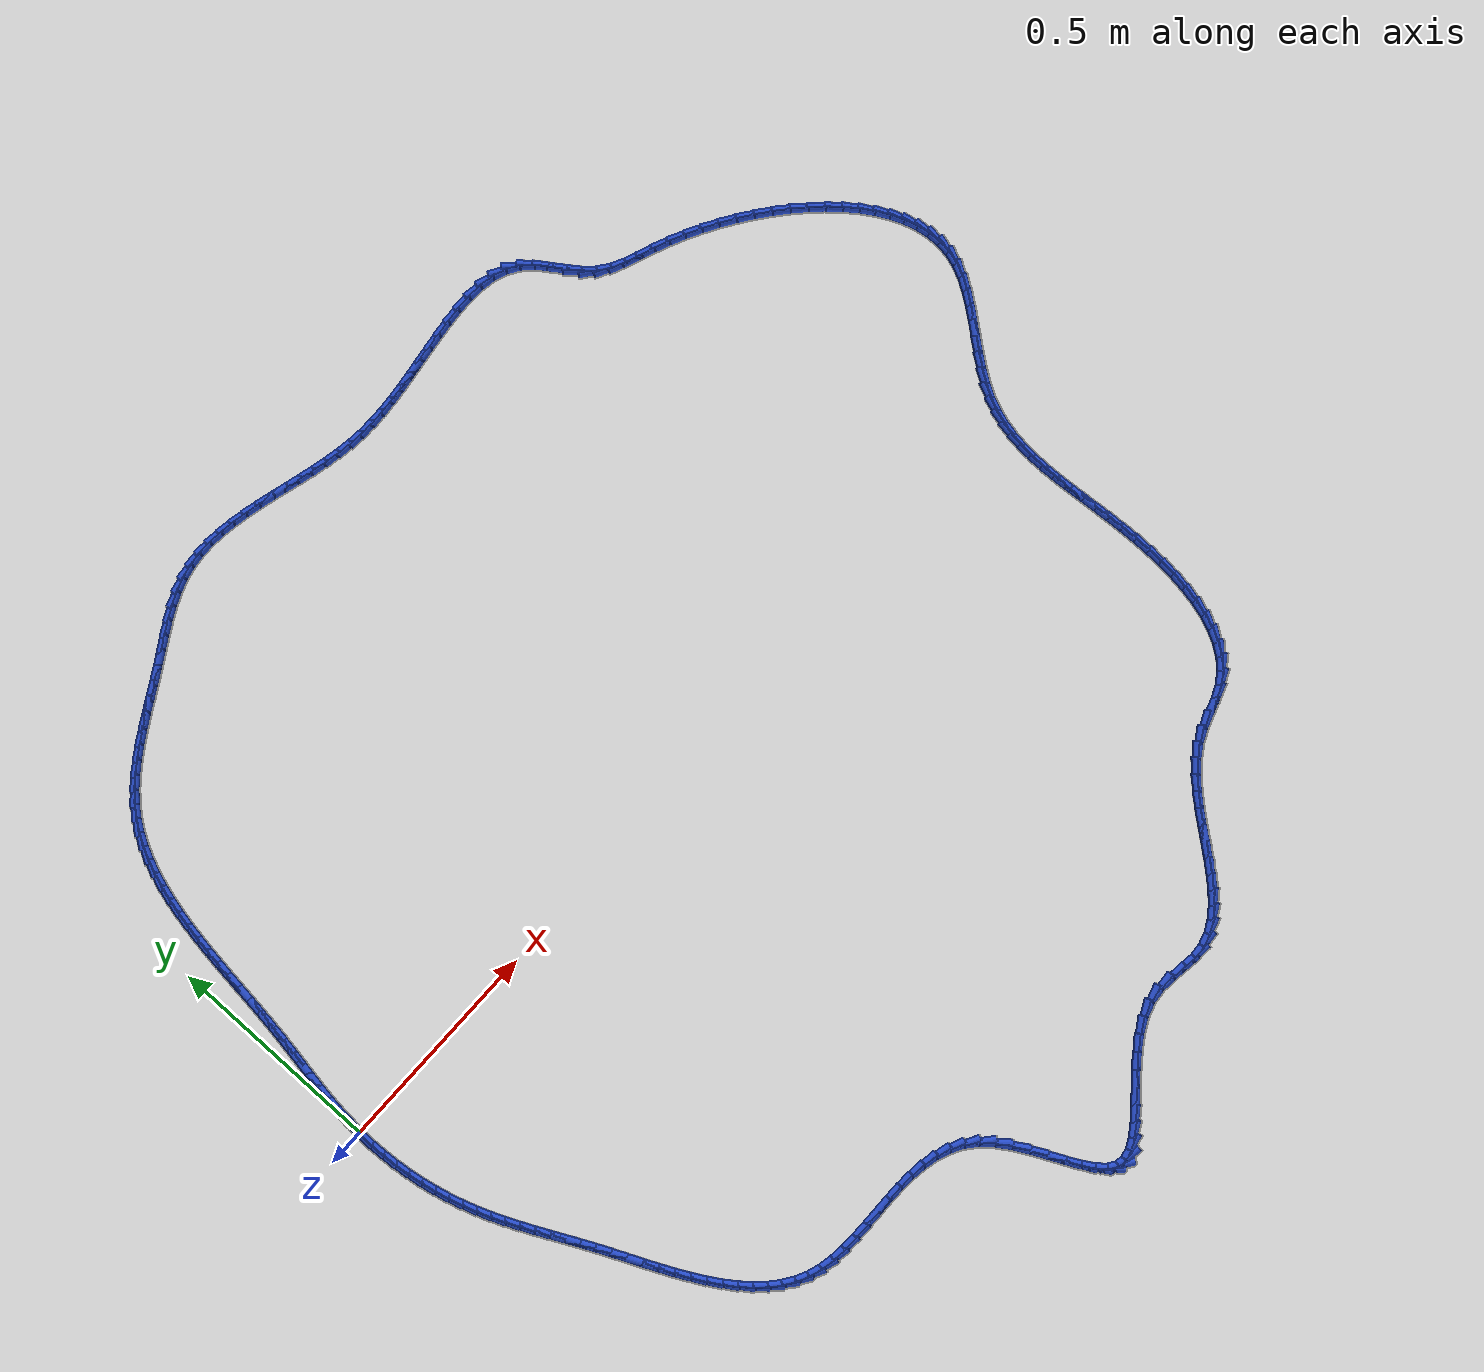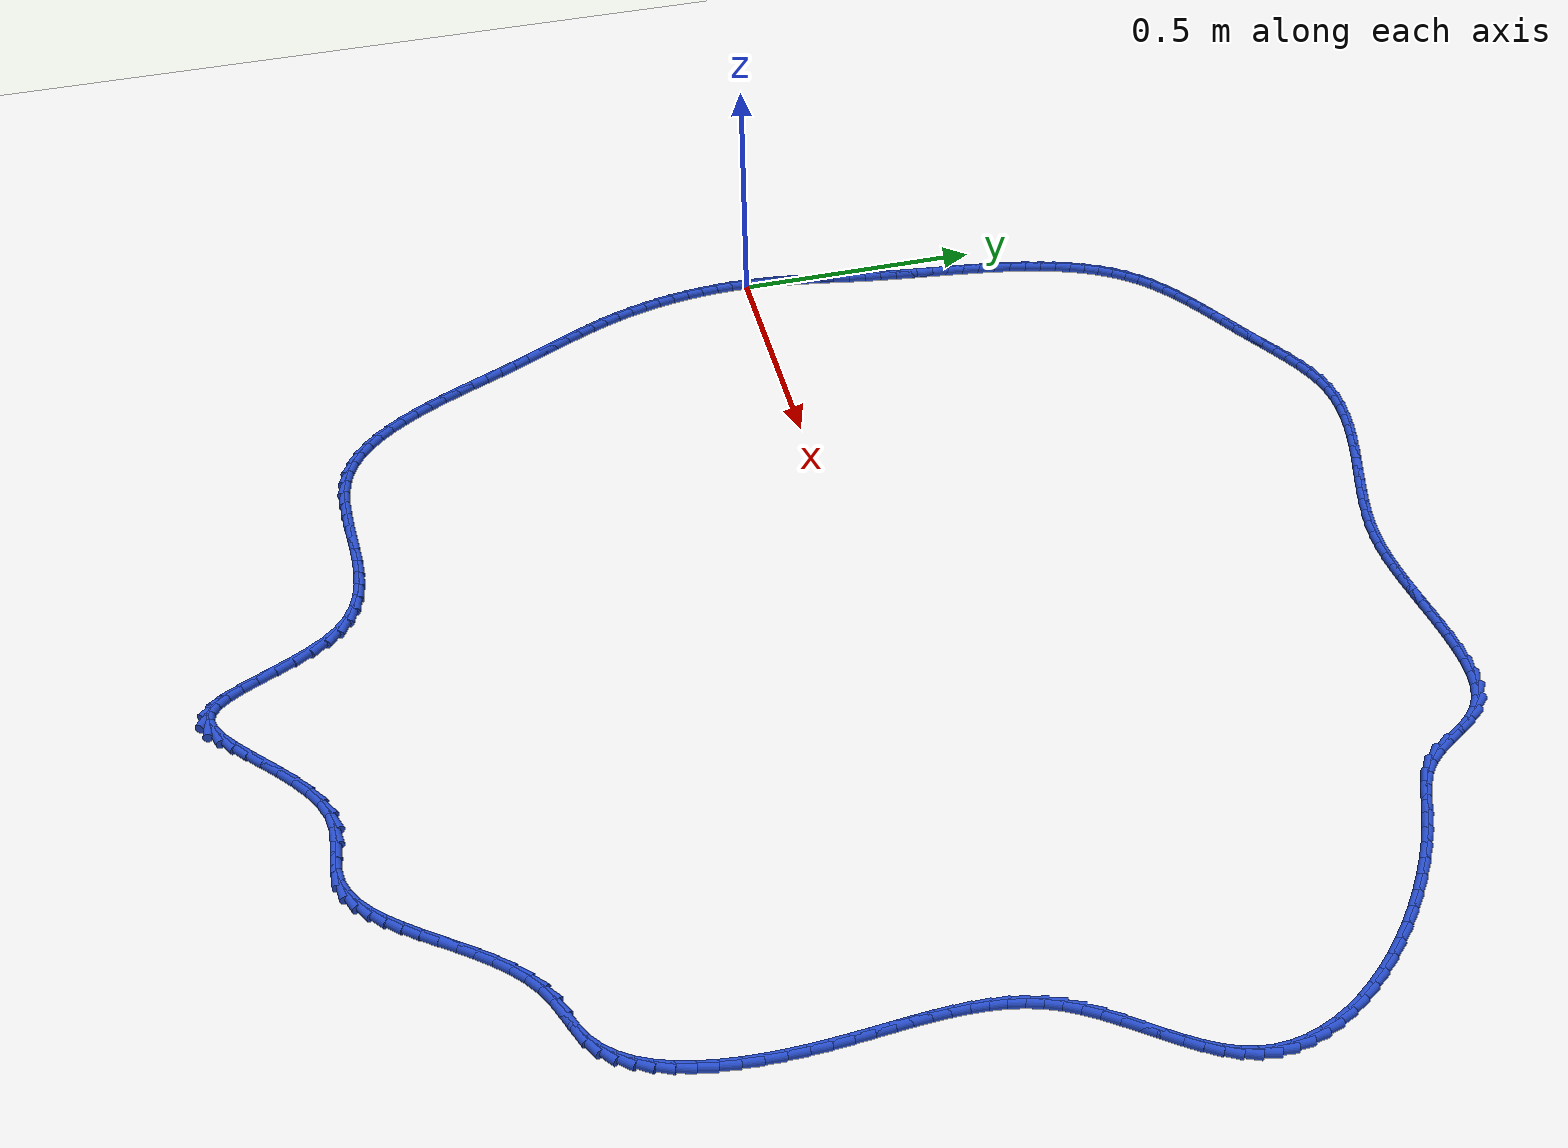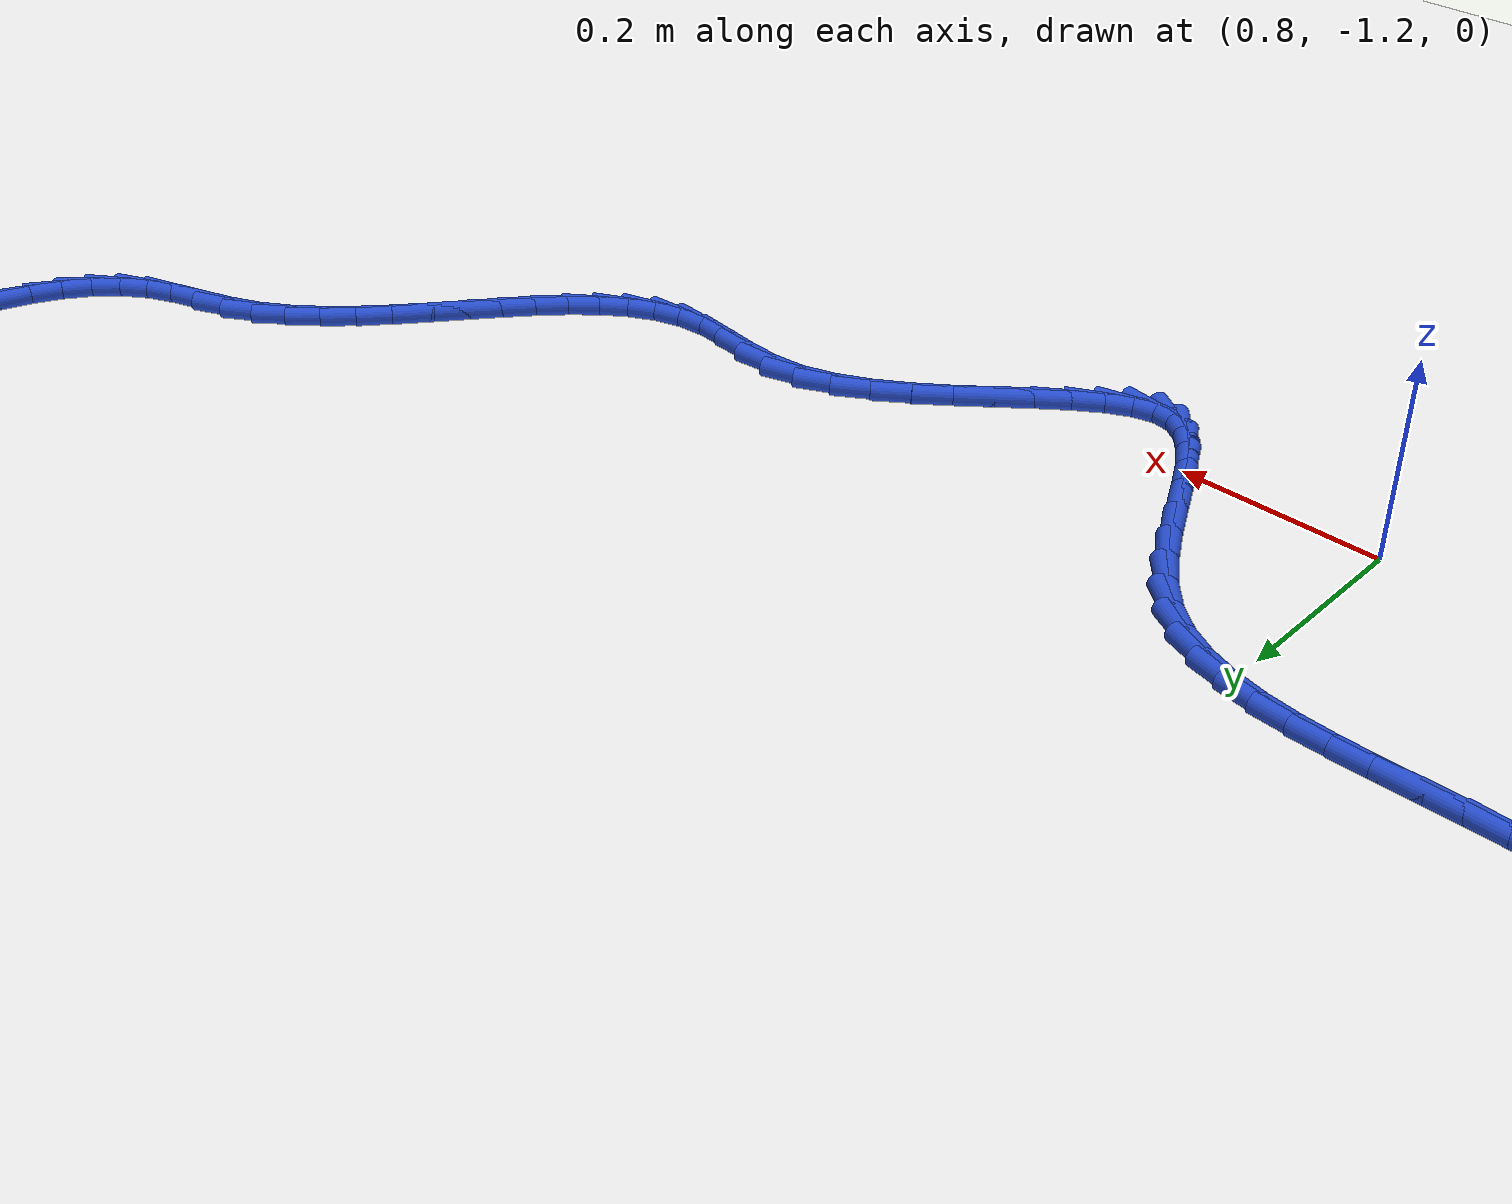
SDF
<sdf version="1.6">
 <world name="default">
  <light name="sun" type="directional">
   <pose>0 0 10 0 -0 0</pose>
   <diffuse>0.8 0.8 0.8 1</diffuse>
   <specular>0.2 0.2 0.2 1</specular>
   <attenuation>
    <range>1000</range>
    <constant>0.9</constant>
    <linear>0.01</linear>
    <quadratic>0.001</quadratic>
   </attenuation>
   <direction>-0.5 0.1 -0.9</direction>
  </light>
  <model name="ground_plane">
   <static>1</static>
   <link name="link">
    <collision name="collision">
     <geometry><plane><normal>0 0 1</normal><size>100 100</size></plane></geometry>
     <surface><friction><ode><mu>100</mu><mu2>50</mu2></ode></friction></surface>
    </collision>
    <visual name="visual">
     <cast_shadows>0</cast_shadows>
     <geometry><plane><normal>0 0 1</normal><size>100 100</size></plane></geometry>
     <material>
      <script><uri>file://media/materials/scripts/gazebo.material</uri><name>Gazebo/WhiteGlow</name></script>
     </material>
    </visual>
   </link>
  </model>
  <gravity>0 0 -9.8</gravity>
  <magnetic_field>6e-06 2.3e-05 -4.2e-05</magnetic_field>
  <atmosphere type="adiabatic"/>
  <physics name="default_physics" default="0" type="ode">
   <max_step_size>0.001</max_step_size>
   <real_time_factor>1</real_time_factor>
   <real_time_update_rate>1000</real_time_update_rate>
  </physics>
  <scene><ambient>0.4 0.4 0.4 1</ambient><background>0.7 0.7 0.7 1</background><shadows>1</shadows></scene>
  <spherical_coordinates>
   <surface_model>EARTH_WGS84</surface_model>
   <latitude_deg>0</latitude_deg>
   <longitude_deg>0</longitude_deg>
   <elevation>0</elevation>
   <heading_deg>0</heading_deg>
  </spherical_coordinates>
  <model name="line">
   <link name="link_0">
    <pose>1.3877787807814457e-17 -4.85722573273506e-17 0.01 0 1.57 1.5098343674166879</pose>
    <collision name="collision">
     <geometry><cylinder><radius>0.01</radius><length>0.08</length></cylinder></geometry>
    </collision>
    <visual name="visual">
     <material>
      <script><name>Gazebo/Blue</name><uri>file://media/materials/scripts/gazebo.material</uri></script>
     </material>
     <geometry><cylinder><radius>0.01</radius><length>0.08</length></cylinder></geometry>
    </visual>
   </link>
   <link name="link_1">
    <pose>0.002005822508972515 0.032862085258667274 0.01 0 1.57 1.471653737826297</pose>
    <collision name="collision">
     <geometry><cylinder><radius>0.01</radius><length>0.08</length></cylinder></geometry>
    </collision>
    <visual name="visual">
     <material>
      <script><name>Gazebo/Blue</name><uri>file://media/materials/scripts/gazebo.material</uri></script>
     </material>
     <geometry><cylinder><radius>0.01</radius><length>0.08</length></cylinder></geometry>
    </visual>
   </link>
   <link name="link_2">
    <pose>0.005251245925880077 0.0654896685566331 0.01 0 1.57 1.440857654034206</pose>
    <collision name="collision">
     <geometry><cylinder><radius>0.01</radius><length>0.08</length></cylinder></geometry>
    </collision>
    <visual name="visual">
     <material>
      <script><name>Gazebo/Blue</name><uri>file://media/materials/scripts/gazebo.material</uri></script>
     </material>
     <geometry><cylinder><radius>0.01</radius><length>0.08</length></cylinder></geometry>
    </visual>
   </link>
   <link name="link_3">
    <pose>0.00949792651968441 0.09798771672754512 0.01 0 1.57 1.4177356766284084</pose>
    <collision name="collision">
     <geometry><cylinder><radius>0.01</radius><length>0.08</length></cylinder></geometry>
    </collision>
    <visual name="visual">
     <material>
      <script><name>Gazebo/Blue</name><uri>file://media/materials/scripts/gazebo.material</uri></script>
     </material>
     <geometry><cylinder><radius>0.01</radius><length>0.08</length></cylinder></geometry>
    </visual>
   </link>
   <link name="link_4">
    <pose>0.014507520559347219 0.13046119660505093 0.01 0 1.57 1.402406037582658</pose>
    <collision name="collision">
     <geometry><cylinder><radius>0.01</radius><length>0.08</length></cylinder></geometry>
    </collision>
    <visual name="visual">
     <material>
      <script><name>Gazebo/Blue</name><uri>file://media/materials/scripts/gazebo.material</uri></script>
     </material>
     <geometry><cylinder><radius>0.01</radius><length>0.08</length></cylinder></geometry>
    </visual>
   </link>
   <link name="link_5">
    <pose>0.020041684313830247 0.16301507502279824 0.01 0 1.57 1.3948543406237481</pose>
    <collision name="collision">
     <geometry><cylinder><radius>0.01</radius><length>0.08</length></cylinder></geometry>
    </collision>
    <visual name="visual">
     <material>
      <script><name>Gazebo/Blue</name><uri>file://media/materials/scripts/gazebo.material</uri></script>
     </material>
     <geometry><cylinder><radius>0.01</radius><length>0.08</length></cylinder></geometry>
    </visual>
   </link>
   <link name="link_6">
    <pose>0.025862074052095164 0.1957543188144347 0.01 0 1.57 1.3949639020550204</pose>
    <collision name="collision">
     <geometry><cylinder><radius>0.01</radius><length>0.08</length></cylinder></geometry>
    </collision>
    <visual name="visual">
     <material>
      <script><name>Gazebo/Blue</name><uri>file://media/materials/scripts/gazebo.material</uri></script>
     </material>
     <geometry><cylinder><radius>0.01</radius><length>0.08</length></cylinder></geometry>
    </visual>
   </link>
   <link name="link_7">
    <pose>0.03173034604310371 0.22878389481360795 0.01 0 1.57 1.4025346439396587</pose>
    <collision name="collision">
     <geometry><cylinder><radius>0.01</radius><length>0.08</length></cylinder></geometry>
    </collision>
    <visual name="visual">
     <material>
      <script><name>Gazebo/Blue</name><uri>file://media/materials/scripts/gazebo.material</uri></script>
     </material>
     <geometry><cylinder><radius>0.01</radius><length>0.08</length></cylinder></geometry>
    </visual>
   </link>
   <link name="link_8">
    <pose>0.0374081565558176 0.2622087698539657 0.01 0 1.57 1.4171275850355238</pose>
    <collision name="collision">
     <geometry><cylinder><radius>0.01</radius><length>0.08</length></cylinder></geometry>
    </collision>
    <visual name="visual">
     <material>
      <script><name>Gazebo/Blue</name><uri>file://media/materials/scripts/gazebo.material</uri></script>
     </material>
     <geometry><cylinder><radius>0.01</radius><length>0.08</length></cylinder></geometry>
    </visual>
   </link>
   <link name="link_9">
    <pose>0.042662340737105536 0.2961308368124762 0.01 0 1.57 1.4329525047710476</pose>
    <collision name="collision">
     <geometry><cylinder><radius>0.01</radius><length>0.08</length></cylinder></geometry>
    </collision>
    <visual name="visual">
     <material>
      <script><name>Gazebo/Blue</name><uri>file://media/materials/scripts/gazebo.material</uri></script>
     </material>
     <geometry><cylinder><radius>0.01</radius><length>0.08</length></cylinder></geometry>
    </visual>
   </link>
   <link name="link_10">
    <pose>0.047436668979368476 0.3305469674998484 0.01 0 1.57 1.4433966388061799</pose>
    <collision name="collision">
     <geometry><cylinder><radius>0.01</radius><length>0.08</length></cylinder></geometry>
    </collision>
    <visual name="visual">
     <material>
      <script><name>Gazebo/Blue</name><uri>file://media/materials/scripts/gazebo.material</uri></script>
     </material>
     <geometry><cylinder><radius>0.01</radius><length>0.08</length></cylinder></geometry>
    </visual>
   </link>
   <link name="link_11">
    <pose>0.0518915634619804 0.36532543864893435 0.01 0 1.57 1.4482997360209395</pose>
    <collision name="collision">
     <geometry><cylinder><radius>0.01</radius><length>0.08</length></cylinder></geometry>
    </collision>
    <visual name="visual">
     <material>
      <script><name>Gazebo/Blue</name><uri>file://media/materials/scripts/gazebo.material</uri></script>
     </material>
     <geometry><cylinder><radius>0.01</radius><length>0.08</length></cylinder></geometry>
    </visual>
   </link>
   <link name="link_12">
    <pose>0.05620067080520865 0.40032667753964574 0.01 0 1.57 1.4478051291439054</pose>
    <collision name="collision">
     <geometry><cylinder><radius>0.01</radius><length>0.08</length></cylinder></geometry>
    </collision>
    <visual name="visual">
     <material>
      <script><name>Gazebo/Blue</name><uri>file://media/materials/scripts/gazebo.material</uri></script>
     </material>
     <geometry><cylinder><radius>0.01</radius><length>0.08</length></cylinder></geometry>
    </visual>
   </link>
   <link name="link_13">
    <pose>0.06053763762932055 0.4354111114518938 0.01 0 1.57 1.4419473533217477</pose>
    <collision name="collision">
     <geometry><cylinder><radius>0.01</radius><length>0.08</length></cylinder></geometry>
    </collision>
    <visual name="visual">
     <material>
      <script><name>Gazebo/Blue</name><uri>file://media/materials/scripts/gazebo.material</uri></script>
     </material>
     <geometry><cylinder><radius>0.01</radius><length>0.08</length></cylinder></geometry>
    </visual>
   </link>
   <link name="link_14">
    <pose>0.06507611055458347 0.47043916766559013 0.01 0 1.57 1.4306550359925612</pose>
    <collision name="collision">
     <geometry><cylinder><radius>0.01</radius><length>0.08</length></cylinder></geometry>
    </collision>
    <visual name="visual">
     <material>
      <script><name>Gazebo/Blue</name><uri>file://media/materials/scripts/gazebo.material</uri></script>
     </material>
     <geometry><cylinder><radius>0.01</radius><length>0.08</length></cylinder></geometry>
    </visual>
   </link>
   <link name="link_15">
    <pose>0.06998973620126477 0.5052712734606467 0.01 0 1.57 1.4137533707198946</pose>
    <collision name="collision">
     <geometry><cylinder><radius>0.01</radius><length>0.08</length></cylinder></geometry>
    </collision>
    <visual name="visual">
     <material>
      <script><name>Gazebo/Blue</name><uri>file://media/materials/scripts/gazebo.material</uri></script>
     </material>
     <geometry><cylinder><radius>0.01</radius><length>0.08</length></cylinder></geometry>
    </visual>
   </link>
   <link name="link_16">
    <pose>0.07545216118963177 0.5397678561169745 0.01 0 1.57 1.3909671234156933</pose>
    <collision name="collision">
     <geometry><cylinder><radius>0.01</radius><length>0.08</length></cylinder></geometry>
    </collision>
    <visual name="visual">
     <material>
      <script><name>Gazebo/Blue</name><uri>file://media/materials/scripts/gazebo.material</uri></script>
     </material>
     <geometry><cylinder><radius>0.01</radius><length>0.08</length></cylinder></geometry>
    </visual>
   </link>
   <link name="link_17">
    <pose>0.08163703213995185 0.5737893429144856 0.01 0 1.57 1.3619261029257712</pose>
    <collision name="collision">
     <geometry><cylinder><radius>0.01</radius><length>0.08</length></cylinder></geometry>
    </collision>
    <visual name="visual">
     <material>
      <script><name>Gazebo/Blue</name><uri>file://media/materials/scripts/gazebo.material</uri></script>
     </material>
     <geometry><cylinder><radius>0.01</radius><length>0.08</length></cylinder></geometry>
    </visual>
   </link>
   <link name="link_18">
    <pose>0.08871799567249235 0.6071961611330909 0.01 0 1.57 1.3261763089187146</pose>
    <collision name="collision">
     <geometry><cylinder><radius>0.01</radius><length>0.08</length></cylinder></geometry>
    </collision>
    <visual name="visual">
     <material>
      <script><name>Gazebo/Blue</name><uri>file://media/materials/scripts/gazebo.material</uri></script>
     </material>
     <geometry><cylinder><radius>0.01</radius><length>0.08</length></cylinder></geometry>
    </visual>
   </link>
   <link name="link_19">
    <pose>0.09686869840752063 0.6398487380527025 0.01 0 1.57 1.2832016281928427</pose>
    <collision name="collision">
     <geometry><cylinder><radius>0.01</radius><length>0.08</length></cylinder></geometry>
    </collision>
    <visual name="visual">
     <material>
      <script><name>Gazebo/Blue</name><uri>file://media/materials/scripts/gazebo.material</uri></script>
     </material>
     <geometry><cylinder><radius>0.01</radius><length>0.08</length></cylinder></geometry>
    </visual>
   </link>
   <link name="link_20">
    <pose>0.106262786965304 0.6716075009532316 0.01 0 1.57 1.232462843104132</pose>
    <collision name="collision">
     <geometry><cylinder><radius>0.01</radius><length>0.08</length></cylinder></geometry>
    </collision>
    <visual name="visual">
     <material>
      <script><name>Gazebo/Blue</name><uri>file://media/materials/scripts/gazebo.material</uri></script>
     </material>
     <geometry><cylinder><radius>0.01</radius><length>0.08</length></cylinder></geometry>
    </visual>
   </link>
   <link name="link_21">
    <pose>0.11707390796610982 0.70233287711459 0.01 0 1.57 1.173462196201212</pose>
    <collision name="collision">
     <geometry><cylinder><radius>0.01</radius><length>0.08</length></cylinder></geometry>
    </collision>
    <visual name="visual">
     <material>
      <script><name>Gazebo/Blue</name><uri>file://media/materials/scripts/gazebo.material</uri></script>
     </material>
     <geometry><cylinder><radius>0.01</radius><length>0.08</length></cylinder></geometry>
    </visual>
   </link>
   <link name="link_22">
    <pose>0.12947570803020547 0.7318852938166892 0.01 0 1.57 1.1058412544207106</pose>
    <collision name="collision">
     <geometry><cylinder><radius>0.01</radius><length>0.08</length></cylinder></geometry>
    </collision>
    <visual name="visual">
     <material>
      <script><name>Gazebo/Blue</name><uri>file://media/materials/scripts/gazebo.material</uri></script>
     </material>
     <geometry><cylinder><radius>0.01</radius><length>0.08</length></cylinder></geometry>
    </visual>
   </link>
   <link name="link_23">
    <pose>0.1436418337778583 0.7601251783394406 0.01 0 1.57 1.029514547674262</pose>
    <collision name="collision">
     <geometry><cylinder><radius>0.01</radius><length>0.08</length></cylinder></geometry>
    </collision>
    <visual name="visual">
     <material>
      <script><name>Gazebo/Blue</name><uri>file://media/materials/scripts/gazebo.material</uri></script>
     </material>
     <geometry><cylinder><radius>0.01</radius><length>0.08</length></cylinder></geometry>
    </visual>
   </link>
   <link name="link_24">
    <pose>0.15974593182933566 0.7869129579627561 0.01 0 1.57 0.944828072040286</pose>
    <collision name="collision">
     <geometry><cylinder><radius>0.01</radius><length>0.08</length></cylinder></geometry>
    </collision>
    <visual name="visual">
     <material>
      <script><name>Gazebo/Blue</name><uri>file://media/materials/scripts/gazebo.material</uri></script>
     </material>
     <geometry><cylinder><radius>0.01</radius><length>0.08</length></cylinder></geometry>
    </visual>
   </link>
   <link name="link_25">
    <pose>0.17796164880490487 0.8121090599665466 0.01 0 1.57 0.852933231577433</pose>
    <collision name="collision">
     <geometry><cylinder><radius>0.01</radius><length>0.08</length></cylinder></geometry>
    </collision>
    <visual name="visual">
     <material>
      <script><name>Gazebo/Blue</name><uri>file://media/materials/scripts/gazebo.material</uri></script>
     </material>
     <geometry><cylinder><radius>0.01</radius><length>0.08</length></cylinder></geometry>
    </visual>
   </link>
   <link name="link_26">
    <pose>0.19845724663704184 0.8355783520005767 0.01 0 1.57 0.7634567779924151</pose>
    <collision name="collision">
     <geometry><cylinder><radius>0.01</radius><length>0.08</length></cylinder></geometry>
    </collision>
    <visual name="visual">
     <material>
      <script><name>Gazebo/Blue</name><uri>file://media/materials/scripts/gazebo.material</uri></script>
     </material>
     <geometry><cylinder><radius>0.01</radius><length>0.08</length></cylinder></geometry>
    </visual>
   </link>
   <link name="link_27">
    <pose>0.22120397209784176 0.8573481661345499 0.01 0 1.57 0.6876047246330469</pose>
    <collision name="collision">
     <geometry><cylinder><radius>0.01</radius><length>0.08</length></cylinder></geometry>
    </collision>
    <visual name="visual">
     <material>
      <script><name>Gazebo/Blue</name><uri>file://media/materials/scripts/gazebo.material</uri></script>
     </material>
     <geometry><cylinder><radius>0.01</radius><length>0.08</length></cylinder></geometry>
    </visual>
   </link>
   <link name="link_28">
    <pose>0.24592404696274023 0.8776511876787778 0.01 0 1.57 0.6258743921532061</pose>
    <collision name="collision">
     <geometry><cylinder><radius>0.01</radius><length>0.08</length></cylinder></geometry>
    </collision>
    <visual name="visual">
     <material>
      <script><name>Gazebo/Blue</name><uri>file://media/materials/scripts/gazebo.material</uri></script>
     </material>
     <geometry><cylinder><radius>0.01</radius><length>0.08</length></cylinder></geometry>
    </visual>
   </link>
   <link name="link_29">
    <pose>0.2723237270608856 0.8967332679263186 0.01 0 1.57 0.5775479767237015</pose>
    <collision name="collision">
     <geometry><cylinder><radius>0.01</radius><length>0.08</length></cylinder></geometry>
    </collision>
    <visual name="visual">
     <material>
      <script><name>Gazebo/Blue</name><uri>file://media/materials/scripts/gazebo.material</uri></script>
     </material>
     <geometry><cylinder><radius>0.01</radius><length>0.08</length></cylinder></geometry>
    </visual>
   </link>
   <link name="link_30">
    <pose>0.3001092682214257 0.9148402581702304 0.01 0 1.57 0.541721054083425</pose>
    <collision name="collision">
     <geometry><cylinder><radius>0.01</radius><length>0.08</length></cylinder></geometry>
    </collision>
    <visual name="visual">
     <material>
      <script><name>Gazebo/Blue</name><uri>file://media/materials/scripts/gazebo.material</uri></script>
     </material>
     <geometry><cylinder><radius>0.01</radius><length>0.08</length></cylinder></geometry>
    </visual>
   </link>
   <link name="link_31">
    <pose>0.3289869262735088 0.9322180097035712 0.01 0 1.57 0.5175349325780471</pose>
    <collision name="collision">
     <geometry><cylinder><radius>0.01</radius><length>0.08</length></cylinder></geometry>
    </collision>
    <visual name="visual">
     <material>
      <script><name>Gazebo/Blue</name><uri>file://media/materials/scripts/gazebo.material</uri></script>
     </material>
     <geometry><cylinder><radius>0.01</radius><length>0.08</length></cylinder></geometry>
    </visual>
   </link>
   <link name="link_32">
    <pose>0.3586629570462829 0.9491123738193991 0.01 0 1.57 0.5043038750434684</pose>
    <collision name="collision">
     <geometry><cylinder><radius>0.01</radius><length>0.08</length></cylinder></geometry>
    </collision>
    <visual name="visual">
     <material>
      <script><name>Gazebo/Blue</name><uri>file://media/materials/scripts/gazebo.material</uri></script>
     </material>
     <geometry><cylinder><radius>0.01</radius><length>0.08</length></cylinder></geometry>
    </visual>
   </link>
   <link name="link_33">
    <pose>0.3888436163688961 0.9657692018107722 0.01 0 1.57 0.5015740202347124</pose>
    <collision name="collision">
     <geometry><cylinder><radius>0.01</radius><length>0.08</length></cylinder></geometry>
    </collision>
    <visual name="visual">
     <material>
      <script><name>Gazebo/Blue</name><uri>file://media/materials/scripts/gazebo.material</uri></script>
     </material>
     <geometry><cylinder><radius>0.01</radius><length>0.08</length></cylinder></geometry>
    </visual>
   </link>
   <link name="link_34">
    <pose>0.4192351600704964 0.9824343449707487 0.01 0 1.57 0.5091422025681815</pose>
    <collision name="collision">
     <geometry><cylinder><radius>0.01</radius><length>0.08</length></cylinder></geometry>
    </collision>
    <visual name="visual">
     <material>
      <script><name>Gazebo/Blue</name><uri>file://media/materials/scripts/gazebo.material</uri></script>
     </material>
     <geometry><cylinder><radius>0.01</radius><length>0.08</length></cylinder></geometry>
    </visual>
   </link>
   <link name="link_35">
    <pose>0.44954384398023184 0.9993536545923862 0.01 0 1.57 0.5226072632514661</pose>
    <collision name="collision">
     <geometry><cylinder><radius>0.01</radius><length>0.08</length></cylinder></geometry>
    </collision>
    <visual name="visual">
     <material>
      <script><name>Gazebo/Blue</name><uri>file://media/materials/scripts/gazebo.material</uri></script>
     </material>
     <geometry><cylinder><radius>0.01</radius><length>0.08</length></cylinder></geometry>
    </visual>
   </link>
   <link name="link_36">
    <pose>0.47954323163416784 1.016634172122781 0.01 0 1.57 0.5224143115743641</pose>
    <collision name="collision">
     <geometry><cylinder><radius>0.01</radius><length>0.08</length></cylinder></geometry>
    </collision>
    <visual name="visual">
     <material>
      <script><name>Gazebo/Blue</name><uri>file://media/materials/scripts/gazebo.material</uri></script>
     </material>
     <geometry><cylinder><radius>0.01</radius><length>0.08</length></cylinder></geometry>
    </visual>
   </link>
   <link name="link_37">
    <pose>0.509304229616162 1.0337697233082912 0.01 0 1.57 0.5026763731914664</pose>
    <collision name="collision">
     <geometry><cylinder><radius>0.01</radius><length>0.08</length></cylinder></geometry>
    </collision>
    <visual name="visual">
     <material>
      <script><name>Gazebo/Blue</name><uri>file://media/materials/scripts/gazebo.material</uri></script>
     </material>
     <geometry><cylinder><radius>0.01</radius><length>0.08</length></cylinder></geometry>
    </visual>
   </link>
   <link name="link_38">
    <pose>0.5389798269954373 1.0500848537686507 0.01 0 1.57 0.462238713212926</pose>
    <collision name="collision">
     <geometry><cylinder><radius>0.01</radius><length>0.08</length></cylinder></geometry>
    </collision>
    <visual name="visual">
     <material>
      <script><name>Gazebo/Blue</name><uri>file://media/materials/scripts/gazebo.material</uri></script>
     </material>
     <geometry><cylinder><radius>0.01</radius><length>0.08</length></cylinder></geometry>
    </visual>
   </link>
   <link name="link_39">
    <pose>0.5687230155376234 1.064904103562747 0.01 0 1.57 0.3994174600707495</pose>
    <collision name="collision">
     <geometry><cylinder><radius>0.01</radius><length>0.08</length></cylinder></geometry>
    </collision>
    <visual name="visual">
     <material>
      <script><name>Gazebo/Blue</name><uri>file://media/materials/scripts/gazebo.material</uri></script>
     </material>
     <geometry><cylinder><radius>0.01</radius><length>0.08</length></cylinder></geometry>
    </visual>
   </link>
   <link name="link_40">
    <pose>0.5986867870083501 1.0775520127494689 0.01 0 1.57 0.31248595396104106</pose>
    <collision name="collision">
     <geometry><cylinder><radius>0.01</radius><length>0.08</length></cylinder></geometry>
    </collision>
    <visual name="visual">
     <material>
      <script><name>Gazebo/Blue</name><uri>file://media/materials/scripts/gazebo.material</uri></script>
     </material>
     <geometry><cylinder><radius>0.01</radius><length>0.08</length></cylinder></geometry>
    </visual>
   </link>
   <link name="link_41">
    <pose>0.6290241331732458 1.0873531213877032 0.01 0 1.57 0.2025114092580881</pose>
    <collision name="collision">
     <geometry><cylinder><radius>0.01</radius><length>0.08</length></cylinder></geometry>
    </collision>
    <visual name="visual">
     <material>
      <script><name>Gazebo/Blue</name><uri>file://media/materials/scripts/gazebo.material</uri></script>
     </material>
     <geometry><cylinder><radius>0.01</radius><length>0.08</length></cylinder></geometry>
    </visual>
   </link>
   <link name="link_42">
    <pose>0.6598770739553411 1.0936880316659074 0.01 0 1.57 0.09165707438052409</pose>
    <collision name="collision">
     <geometry><cylinder><radius>0.01</radius><length>0.08</length></cylinder></geometry>
    </collision>
    <visual name="visual">
     <material>
      <script><name>Gazebo/Blue</name><uri>file://media/materials/scripts/gazebo.material</uri></script>
     </material>
     <geometry><cylinder><radius>0.01</radius><length>0.08</length></cylinder></geometry>
    </visual>
   </link>
   <link name="link_43">
    <pose>0.6912632497832496 1.0965728798013883 0.01 0 1.57 -0.004602035497805699</pose>
    <collision name="collision">
     <geometry><cylinder><radius>0.01</radius><length>0.08</length></cylinder></geometry>
    </collision>
    <visual name="visual">
     <material>
      <script><name>Gazebo/Blue</name><uri>file://media/materials/scripts/gazebo.material</uri></script>
     </material>
     <geometry><cylinder><radius>0.01</radius><length>0.08</length></cylinder></geometry>
    </visual>
   </link>
   <link name="link_44">
    <pose>0.7231215354477635 1.0964262658048267 0.01 0 1.57 -0.08511363219749522</pose>
    <collision name="collision">
     <geometry><cylinder><radius>0.01</radius><length>0.08</length></cylinder></geometry>
    </collision>
    <visual name="visual">
     <material>
      <script><name>Gazebo/Blue</name><uri>file://media/materials/scripts/gazebo.material</uri></script>
     </material>
     <geometry><cylinder><radius>0.01</radius><length>0.08</length></cylinder></geometry>
    </visual>
   </link>
   <link name="link_45">
    <pose>0.7553895578639738 1.0936731658783725 0.01 0 1.57 -0.15015815287526973</pose>
    <collision name="collision">
     <geometry><cylinder><radius>0.01</radius><length>0.08</length></cylinder></geometry>
    </collision>
    <visual name="visual">
     <material>
      <script><name>Gazebo/Blue</name><uri>file://media/materials/scripts/gazebo.material</uri></script>
     </material>
     <geometry><cylinder><radius>0.01</radius><length>0.08</length></cylinder></geometry>
    </visual>
   </link>
   <link name="link_46">
    <pose>0.7880049439469723 1.0887385562241763 0.01 0 1.57 -0.2006394845438224</pose>
    <collision name="collision">
     <geometry><cylinder><radius>0.01</radius><length>0.08</length></cylinder></geometry>
    </collision>
    <visual name="visual">
     <material>
      <script><name>Gazebo/Blue</name><uri>file://media/materials/scripts/gazebo.material</uri></script>
     </material>
     <geometry><cylinder><radius>0.01</radius><length>0.08</length></cylinder></geometry>
    </visual>
   </link>
   <link name="link_47">
    <pose>0.820905320611851 1.082047413044388 0.01 0 1.57 -0.2376329992822089</pose>
    <collision name="collision">
     <geometry><cylinder><radius>0.01</radius><length>0.08</length></cylinder></geometry>
    </collision>
    <visual name="visual">
     <material>
      <script><name>Gazebo/Blue</name><uri>file://media/materials/scripts/gazebo.material</uri></script>
     </material>
     <geometry><cylinder><radius>0.01</radius><length>0.08</length></cylinder></geometry>
    </visual>
   </link>
   <link name="link_48">
    <pose>0.8540283147737013 1.0740247125411582 0.01 0 1.57 -0.26210953408189924</pose>
    <collision name="collision">
     <geometry><cylinder><radius>0.01</radius><length>0.08</length></cylinder></geometry>
    </collision>
    <visual name="visual">
     <material>
      <script><name>Gazebo/Blue</name><uri>file://media/materials/scripts/gazebo.material</uri></script>
     </material>
     <geometry><cylinder><radius>0.01</radius><length>0.08</length></cylinder></geometry>
    </visual>
   </link>
   <link name="link_49">
    <pose>0.8873115533476147 1.065095430916636 0.01 0 1.57 -0.2747905617515638</pose>
    <collision name="collision">
     <geometry><cylinder><radius>0.01</radius><length>0.08</length></cylinder></geometry>
    </collision>
    <visual name="visual">
     <material>
      <script><name>Gazebo/Blue</name><uri>file://media/materials/scripts/gazebo.material</uri></script>
     </material>
     <geometry><cylinder><radius>0.01</radius><length>0.08</length></cylinder></geometry>
    </visual>
   </link>
   <link name="link_50">
    <pose>0.9206926632486832 1.0556845443729725 0.01 0 1.57 -0.2760825117288324</pose>
    <collision name="collision">
     <geometry><cylinder><radius>0.01</radius><length>0.08</length></cylinder></geometry>
    </collision>
    <visual name="visual">
     <material>
      <script><name>Gazebo/Blue</name><uri>file://media/materials/scripts/gazebo.material</uri></script>
     </material>
     <geometry><cylinder><radius>0.01</radius><length>0.08</length></cylinder></geometry>
    </visual>
   </link>
   <link name="link_51">
    <pose>0.9541092713919975 1.0462170291123174 0.01 0 1.57 -0.2660534748109831</pose>
    <collision name="collision">
     <geometry><cylinder><radius>0.01</radius><length>0.08</length></cylinder></geometry>
    </collision>
    <visual name="visual">
     <material>
      <script><name>Gazebo/Blue</name><uri>file://media/materials/scripts/gazebo.material</uri></script>
     </material>
     <geometry><cylinder><radius>0.01</radius><length>0.08</length></cylinder></geometry>
    </visual>
   </link>
   <link name="link_52">
    <pose>0.9874990046926504 1.0371178613368208 0.01 0 1.57 -0.24443375308970214</pose>
    <collision name="collision">
     <geometry><cylinder><radius>0.01</radius><length>0.08</length></cylinder></geometry>
    </collision>
    <visual name="visual">
     <material>
      <script><name>Gazebo/Blue</name><uri>file://media/materials/scripts/gazebo.material</uri></script>
     </material>
     <geometry><cylinder><radius>0.01</radius><length>0.08</length></cylinder></geometry>
    </visual>
   </link>
   <link name="link_53">
    <pose>1.020799490065733 1.028812017248633 0.01 0 1.57 -0.21063804163629843</pose>
    <collision name="collision">
     <geometry><cylinder><radius>0.01</radius><length>0.08</length></cylinder></geometry>
    </collision>
    <visual name="visual">
     <material>
      <script><name>Gazebo/Blue</name><uri>file://media/materials/scripts/gazebo.material</uri></script>
     </material>
     <geometry><cylinder><radius>0.01</radius><length>0.08</length></cylinder></geometry>
    </visual>
   </link>
   <link name="link_54">
    <pose>1.0539483544263364 1.0217244730499042 0.01 0 1.57 -0.1638226156804178</pose>
    <collision name="collision">
     <geometry><cylinder><radius>0.01</radius><length>0.08</length></cylinder></geometry>
    </collision>
    <visual name="visual">
     <material>
      <script><name>Gazebo/Blue</name><uri>file://media/materials/scripts/gazebo.material</uri></script>
     </material>
     <geometry><cylinder><radius>0.01</radius><length>0.08</length></cylinder></geometry>
    </visual>
   </link>
   <link name="link_55">
    <pose>1.086883224689553 1.0162802049427844 0.01 0 1.57 -0.10352199797164098</pose>
    <collision name="collision">
     <geometry><cylinder><radius>0.01</radius><length>0.08</length></cylinder></geometry>
    </collision>
    <visual name="visual">
     <material>
      <script><name>Gazebo/Blue</name><uri>file://media/materials/scripts/gazebo.material</uri></script>
     </material>
     <geometry><cylinder><radius>0.01</radius><length>0.08</length></cylinder></geometry>
    </visual>
   </link>
   <link name="link_56">
    <pose>1.119546195399658 1.0128867379117057 0.01 0 1.57 -0.04022461310720023</pose>
    <collision name="collision">
     <geometry><cylinder><radius>0.01</radius><length>0.08</length></cylinder></geometry>
    </collision>
    <visual name="visual">
     <material>
      <script><name>Gazebo/Blue</name><uri>file://media/materials/scripts/gazebo.material</uri></script>
     </material>
     <geometry><cylinder><radius>0.01</radius><length>0.08</length></cylinder></geometry>
    </visual>
   </link>
   <link name="link_57">
    <pose>1.151974073827715 1.011581635078166 0.01 0 1.57 0.014464242559410612</pose>
    <collision name="collision">
     <geometry><cylinder><radius>0.01</radius><length>0.08</length></cylinder></geometry>
    </collision>
    <visual name="visual">
     <material>
      <script><name>Gazebo/Blue</name><uri>file://media/materials/scripts/gazebo.material</uri></script>
     </material>
     <geometry><cylinder><radius>0.01</radius><length>0.08</length></cylinder></geometry>
    </visual>
   </link>
   <link name="link_58">
    <pose>1.1842941162014746 1.0120491526148319 0.01 0 1.57 0.05899436904600479</pose>
    <collision name="collision">
     <geometry><cylinder><radius>0.01</radius><length>0.08</length></cylinder></geometry>
    </collision>
    <visual name="visual">
     <material>
      <script><name>Gazebo/Blue</name><uri>file://media/materials/scripts/gazebo.material</uri></script>
     </material>
     <geometry><cylinder><radius>0.01</radius><length>0.08</length></cylinder></geometry>
    </visual>
   </link>
   <link name="link_59">
    <pose>1.2166371930566153 1.0139594286751834 0.01 0 1.57 0.09276235101335384</pose>
    <collision name="collision">
     <geometry><cylinder><radius>0.01</radius><length>0.08</length></cylinder></geometry>
    </collision>
    <visual name="visual">
     <material>
      <script><name>Gazebo/Blue</name><uri>file://media/materials/scripts/gazebo.material</uri></script>
     </material>
     <geometry><cylinder><radius>0.01</radius><length>0.08</length></cylinder></geometry>
    </visual>
   </link>
   <link name="link_60">
    <pose>1.249134174928815 1.016982601412701 0.01 0 1.57 0.11558992344600376</pose>
    <collision name="collision">
     <geometry><cylinder><radius>0.01</radius><length>0.08</length></cylinder></geometry>
    </collision>
    <visual name="visual">
     <material>
      <script><name>Gazebo/Blue</name><uri>file://media/materials/scripts/gazebo.material</uri></script>
     </material>
     <geometry><cylinder><radius>0.01</radius><length>0.08</length></cylinder></geometry>
    </visual>
   </link>
   <link name="link_61">
    <pose>1.2819159323537523 1.0207888089808654 0.01 0 1.57 0.12760744909594707</pose>
    <collision name="collision">
     <geometry><cylinder><radius>0.01</radius><length>0.08</length></cylinder></geometry>
    </collision>
    <visual name="visual">
     <material>
      <script><name>Gazebo/Blue</name><uri>file://media/materials/scripts/gazebo.material</uri></script>
     </material>
     <geometry><cylinder><radius>0.01</radius><length>0.08</length></cylinder></geometry>
    </visual>
   </link>
   <link name="link_62">
    <pose>1.3151133358671043 1.0250481895331567 0.01 0 1.57 0.1291579099587101</pose>
    <collision name="collision">
     <geometry><cylinder><radius>0.01</radius><length>0.08</length></cylinder></geometry>
    </collision>
    <visual name="visual">
     <material>
      <script><name>Gazebo/Blue</name><uri>file://media/materials/scripts/gazebo.material</uri></script>
     </material>
     <geometry><cylinder><radius>0.01</radius><length>0.08</length></cylinder></geometry>
    </visual>
   </link>
   <link name="link_63">
    <pose>1.3488572560045509 1.029430881223056 0.01 0 1.57 0.12073422066357245</pose>
    <collision name="collision">
     <geometry><cylinder><radius>0.01</radius><length>0.08</length></cylinder></geometry>
    </collision>
    <visual name="visual">
     <material>
      <script><name>Gazebo/Blue</name><uri>file://media/materials/scripts/gazebo.material</uri></script>
     </material>
     <geometry><cylinder><radius>0.01</radius><length>0.08</length></cylinder></geometry>
    </visual>
   </link>
   <link name="link_64">
    <pose>1.383278563301769 1.033607022204043 0.01 0 1.57 0.10286352939975</pose>
    <collision name="collision">
     <geometry><cylinder><radius>0.01</radius><length>0.08</length></cylinder></geometry>
    </collision>
    <visual name="visual">
     <material>
      <script><name>Gazebo/Blue</name><uri>file://media/materials/scripts/gazebo.material</uri></script>
     </material>
     <geometry><cylinder><radius>0.01</radius><length>0.08</length></cylinder></geometry>
    </visual>
   </link>
   <link name="link_65">
    <pose>1.418502255923918 1.037243088893848 0.01 0 1.57 0.07096598074154586</pose>
    <collision name="collision">
     <geometry><cylinder><radius>0.01</radius><length>0.08</length></cylinder></geometry>
    </collision>
    <visual name="visual">
     <material>
      <script><name>Gazebo/Blue</name><uri>file://media/materials/scripts/gazebo.material</uri></script>
     </material>
     <geometry><cylinder><radius>0.01</radius><length>0.08</length></cylinder></geometry>
    </visual>
   </link>
   <link name="link_66">
    <pose>1.4543046116999094 1.0397881120095163 0.01 0 1.57 0.015924536040777683</pose>
    <collision name="collision">
     <geometry><cylinder><radius>0.01</radius><length>0.08</length></cylinder></geometry>
    </collision>
    <visual name="visual">
     <material>
      <script><name>Gazebo/Blue</name><uri>file://media/materials/scripts/gazebo.material</uri></script>
     </material>
     <geometry><cylinder><radius>0.01</radius><length>0.08</length></cylinder></geometry>
    </visual>
   </link>
   <link name="link_67">
    <pose>1.4899234643043502 1.0403553736631455 0.01 0 1.57 -0.06707057663341108</pose>
    <collision name="collision">
     <geometry><cylinder><radius>0.01</radius><length>0.08</length></cylinder></geometry>
    </collision>
    <visual name="visual">
     <material>
      <script><name>Gazebo/Blue</name><uri>file://media/materials/scripts/gazebo.material</uri></script>
     </material>
     <geometry><cylinder><radius>0.01</radius><length>0.08</length></cylinder></geometry>
    </visual>
   </link>
   <link name="link_68">
    <pose>1.524550571003348 1.0380294248723434 0.01 0 1.57 -0.18474530111922033</pose>
    <collision name="collision">
     <geometry><cylinder><radius>0.01</radius><length>0.08</length></cylinder></geometry>
    </collision>
    <visual name="visual">
     <material>
      <script><name>Gazebo/Blue</name><uri>file://media/materials/scripts/gazebo.material</uri></script>
     </material>
     <geometry><cylinder><radius>0.01</radius><length>0.08</length></cylinder></geometry>
    </visual>
   </link>
   <link name="link_69">
    <pose>1.5573776890630096 1.031894816654718 0.01 0 1.57 -0.34496713228594533</pose>
    <collision name="collision">
     <geometry><cylinder><radius>0.01</radius><length>0.08</length></cylinder></geometry>
    </collision>
    <visual name="visual">
     <material>
      <script><name>Gazebo/Blue</name><uri>file://media/materials/scripts/gazebo.material</uri></script>
     </material>
     <geometry><cylinder><radius>0.01</radius><length>0.08</length></cylinder></geometry>
    </visual>
   </link>
   <link name="link_70">
    <pose>1.587596575749442 1.0210361000278765 0.01 0 1.57 -0.5517762470682908</pose>
    <collision name="collision">
     <geometry><cylinder><radius>0.01</radius><length>0.08</length></cylinder></geometry>
    </collision>
    <visual name="visual">
     <material>
      <script><name>Gazebo/Blue</name><uri>file://media/materials/scripts/gazebo.material</uri></script>
     </material>
     <geometry><cylinder><radius>0.01</radius><length>0.08</length></cylinder></geometry>
    </visual>
   </link>
   <link name="link_71">
    <pose>1.6143989884810848 1.0045378262227045 0.01 0 1.57 -0.7742431588048644</pose>
    <collision name="collision">
     <geometry><cylinder><radius>0.01</radius><length>0.08</length></cylinder></geometry>
    </collision>
    <visual name="visual">
     <material>
      <script><name>Gazebo/Blue</name><uri>file://media/materials/scripts/gazebo.material</uri></script>
     </material>
     <geometry><cylinder><radius>0.01</radius><length>0.08</length></cylinder></geometry>
    </visual>
   </link>
   <link name="link_72">
    <pose>1.637386166864286 0.9820578551387614 0.01 0 1.57 -0.9163974651949578</pose>
    <collision name="collision">
     <geometry><cylinder><radius>0.01</radius><length>0.08</length></cylinder></geometry>
    </collision>
    <visual name="visual">
     <material>
      <script><name>Gazebo/Blue</name><uri>file://media/materials/scripts/gazebo.material</uri></script>
     </material>
     <geometry><cylinder><radius>0.01</radius><length>0.08</length></cylinder></geometry>
    </visual>
   </link>
   <link name="link_73">
    <pose>1.6577620693705195 0.9554979846195716 0.01 0 1.57 -0.9689745222730514</pose>
    <collision name="collision">
     <geometry><cylinder><radius>0.01</radius><length>0.08</length></cylinder></geometry>
    </collision>
    <visual name="visual">
     <material>
      <script><name>Gazebo/Blue</name><uri>file://media/materials/scripts/gazebo.material</uri></script>
     </material>
     <geometry><cylinder><radius>0.01</radius><length>0.08</length></cylinder></geometry>
    </visual>
   </link>
   <link name="link_74">
    <pose>1.6771227201328682 0.9273089366111642 0.01 0 1.57 -0.9410976311905007</pose>
    <collision name="collision">
     <geometry><cylinder><radius>0.01</radius><length>0.08</length></cylinder></geometry>
    </collision>
    <visual name="visual">
     <material>
      <script><name>Gazebo/Blue</name><uri>file://media/materials/scripts/gazebo.material</uri></script>
     </material>
     <geometry><cylinder><radius>0.01</radius><length>0.08</length></cylinder></geometry>
    </visual>
   </link>
   <link name="link_75">
    <pose>1.6970641432844162 0.8999414330595716 0.01 0 1.57 -0.8281522194897697</pose>
    <collision name="collision">
     <geometry><cylinder><radius>0.01</radius><length>0.08</length></cylinder></geometry>
    </collision>
    <visual name="visual">
     <material>
      <script><name>Gazebo/Blue</name><uri>file://media/materials/scripts/gazebo.material</uri></script>
     </material>
     <geometry><cylinder><radius>0.01</radius><length>0.08</length></cylinder></geometry>
    </visual>
   </link>
   <link name="link_76">
    <pose>1.7191823629582477 0.875846195910824 0.01 0 1.57 -0.6412500001980409</pose>
    <collision name="collision">
     <geometry><cylinder><radius>0.01</radius><length>0.08</length></cylinder></geometry>
    </collision>
    <visual name="visual">
     <material>
      <script><name>Gazebo/Blue</name><uri>file://media/materials/scripts/gazebo.material</uri></script>
     </material>
     <geometry><cylinder><radius>0.01</radius><length>0.08</length></cylinder></geometry>
    </visual>
   </link>
   <link name="link_77">
    <pose>1.744701683008231 0.8567963152979005 0.01 0 1.57 -0.48511577942105033</pose>
    <collision name="collision">
     <geometry><cylinder><radius>0.01</radius><length>0.08</length></cylinder></geometry>
    </collision>
    <visual name="visual">
     <material>
      <script><name>Gazebo/Blue</name><uri>file://media/materials/scripts/gazebo.material</uri></script>
     </material>
     <geometry><cylinder><radius>0.01</radius><length>0.08</length></cylinder></geometry>
    </visual>
   </link>
   <link name="link_78">
    <pose>1.7732895438286342 0.841726778974668 0.01 0 1.57 -0.39521307242148573</pose>
    <collision name="collision">
     <geometry><cylinder><radius>0.01</radius><length>0.08</length></cylinder></geometry>
    </collision>
    <visual name="visual">
     <material>
      <script><name>Gazebo/Blue</name><uri>file://media/materials/scripts/gazebo.material</uri></script>
     </material>
     <geometry><cylinder><radius>0.01</radius><length>0.08</length></cylinder></geometry>
    </visual>
   </link>
   <link name="link_79">
    <pose>1.8042058587016687 0.8288296683989094 0.01 0 1.57 -0.36799917022150597</pose>
    <collision name="collision">
     <geometry><cylinder><radius>0.01</radius><length>0.08</length></cylinder></geometry>
    </collision>
    <visual name="visual">
     <material>
      <script><name>Gazebo/Blue</name><uri>file://media/materials/scripts/gazebo.material</uri></script>
     </material>
     <geometry><cylinder><radius>0.01</radius><length>0.08</length></cylinder></geometry>
    </visual>
   </link>
   <link name="link_80">
    <pose>1.8367105395071817 0.8162970624719484 0.01 0 1.57 -0.39470509530401404</pose>
    <collision name="collision">
     <geometry><cylinder><radius>0.01</radius><length>0.08</length></cylinder></geometry>
    </collision>
    <visual name="visual">
     <material>
      <script><name>Gazebo/Blue</name><uri>file://media/materials/scripts/gazebo.material</uri></script>
     </material>
     <geometry><cylinder><radius>0.01</radius><length>0.08</length></cylinder></geometry>
    </visual>
   </link>
   <link name="link_81">
    <pose>1.8700810052093995 0.8023960706970212 0.01 0 1.57 -0.4410428746394001</pose>
    <collision name="collision">
     <geometry><cylinder><radius>0.01</radius><length>0.08</length></cylinder></geometry>
    </collision>
    <visual name="visual">
     <material>
      <script><name>Gazebo/Blue</name><uri>file://media/materials/scripts/gazebo.material</uri></script>
     </material>
     <geometry><cylinder><radius>0.01</radius><length>0.08</length></cylinder></geometry>
    </visual>
   </link>
   <link name="link_82">
    <pose>1.9038431029294347 0.7864584980878045 0.01 0 1.57 -0.4851297863235632</pose>
    <collision name="collision">
     <geometry><cylinder><radius>0.01</radius><length>0.08</length></cylinder></geometry>
    </collision>
    <visual name="visual">
     <material>
      <script><name>Gazebo/Blue</name><uri>file://media/materials/scripts/gazebo.material</uri></script>
     </material>
     <geometry><cylinder><radius>0.01</radius><length>0.08</length></cylinder></geometry>
    </visual>
   </link>
   <link name="link_83">
    <pose>1.9377072284513568 0.7686070750320387 0.01 0 1.57 -0.5275555047467497</pose>
    <collision name="collision">
     <geometry><cylinder><radius>0.01</radius><length>0.08</length></cylinder></geometry>
    </collision>
    <visual name="visual">
     <material>
      <script><name>Gazebo/Blue</name><uri>file://media/materials/scripts/gazebo.material</uri></script>
     </material>
     <geometry><cylinder><radius>0.01</radius><length>0.08</length></cylinder></geometry>
    </visual>
   </link>
   <link name="link_84">
    <pose>1.971388153850523 0.7489832875116139 0.01 0 1.57 -0.5692847325259838</pose>
    <collision name="collision">
     <geometry><cylinder><radius>0.01</radius><length>0.08</length></cylinder></geometry>
    </collision>
    <visual name="visual">
     <material>
      <script><name>Gazebo/Blue</name><uri>file://media/materials/scripts/gazebo.material</uri></script>
     </material>
     <geometry><cylinder><radius>0.01</radius><length>0.08</length></cylinder></geometry>
    </visual>
   </link>
   <link name="link_85">
    <pose>2.004600651202291 0.7277286215084185 0.01 0 1.57 -0.6111986739123142</pose>
    <collision name="collision">
     <geometry><cylinder><radius>0.01</radius><length>0.08</length></cylinder></geometry>
    </collision>
    <visual name="visual">
     <material>
      <script><name>Gazebo/Blue</name><uri>file://media/materials/scripts/gazebo.material</uri></script>
     </material>
     <geometry><cylinder><radius>0.01</radius><length>0.08</length></cylinder></geometry>
    </visual>
   </link>
   <link name="link_86">
    <pose>2.037059492582018 0.7049845630043429 0.01 0 1.57 -0.6541494897330753</pose>
    <collision name="collision">
     <geometry><cylinder><radius>0.01</radius><length>0.08</length></cylinder></geometry>
    </collision>
    <visual name="visual">
     <material>
      <script><name>Gazebo/Blue</name><uri>file://media/materials/scripts/gazebo.material</uri></script>
     </material>
     <geometry><cylinder><radius>0.01</radius><length>0.08</length></cylinder></geometry>
    </visual>
   </link>
   <link name="link_87">
    <pose>2.0684794500650603 0.6808925979812757 0.01 0 1.57 -0.6990079537516871</pose>
    <collision name="collision">
     <geometry><cylinder><radius>0.01</radius><length>0.08</length></cylinder></geometry>
    </collision>
    <visual name="visual">
     <material>
      <script><name>Gazebo/Blue</name><uri>file://media/materials/scripts/gazebo.material</uri></script>
     </material>
     <geometry><cylinder><radius>0.01</radius><length>0.08</length></cylinder></geometry>
    </visual>
   </link>
   <link name="link_88">
    <pose>2.0985752957267754 0.6555942124211066 0.01 0 1.57 -0.7467084090026327</pose>
    <collision name="collision">
     <geometry><cylinder><radius>0.01</radius><length>0.08</length></cylinder></geometry>
    </collision>
    <visual name="visual">
     <material>
      <script><name>Gazebo/Blue</name><uri>file://media/materials/scripts/gazebo.material</uri></script>
     </material>
     <geometry><cylinder><radius>0.01</radius><length>0.08</length></cylinder></geometry>
    </visual>
   </link>
   <link name="link_89">
    <pose>2.127061801642521 0.6292308923057248 0.01 0 1.57 -0.7982936459995622</pose>
    <collision name="collision">
     <geometry><cylinder><radius>0.01</radius><length>0.08</length></cylinder></geometry>
    </collision>
    <visual name="visual">
     <material>
      <script><name>Gazebo/Blue</name><uri>file://media/materials/scripts/gazebo.material</uri></script>
     </material>
     <geometry><cylinder><radius>0.01</radius><length>0.08</length></cylinder></geometry>
    </visual>
   </link>
   <link name="link_90">
    <pose>2.1536537398876536 0.6019441236170201 0.01 0 1.57 -0.8549604341104302</pose>
    <collision name="collision">
     <geometry><cylinder><radius>0.01</radius><length>0.08</length></cylinder></geometry>
    </collision>
    <visual name="visual">
     <material>
      <script><name>Gazebo/Blue</name><uri>file://media/materials/scripts/gazebo.material</uri></script>
     </material>
     <geometry><cylinder><radius>0.01</radius><length>0.08</length></cylinder></geometry>
    </visual>
   </link>
   <link name="link_91">
    <pose>2.178065882537531 0.5738753923368812 0.01 0 1.57 -0.9181031506975984</pose>
    <collision name="collision">
     <geometry><cylinder><radius>0.01</radius><length>0.08</length></cylinder></geometry>
    </collision>
    <visual name="visual">
     <material>
      <script><name>Gazebo/Blue</name><uri>file://media/materials/scripts/gazebo.material</uri></script>
     </material>
     <geometry><cylinder><radius>0.01</radius><length>0.08</length></cylinder></geometry>
    </visual>
   </link>
   <link name="link_92">
    <pose>2.200013001667511 0.5451661844471984 0.01 0 1.57 -0.98934659656645</pose>
    <collision name="collision">
     <geometry><cylinder><radius>0.01</radius><length>0.08</length></cylinder></geometry>
    </collision>
    <visual name="visual">
     <material>
      <script><name>Gazebo/Blue</name><uri>file://media/materials/scripts/gazebo.material</uri></script>
     </material>
     <geometry><cylinder><radius>0.01</radius><length>0.08</length></cylinder></geometry>
    </visual>
   </link>
   <link name="link_93">
    <pose>2.2192098693529485 0.5159579859298599 0.01 0 1.57 -1.0705470459926498</pose>
    <collision name="collision">
     <geometry><cylinder><radius>0.01</radius><length>0.08</length></cylinder></geometry>
    </collision>
    <visual name="visual">
     <material>
      <script><name>Gazebo/Blue</name><uri>file://media/materials/scripts/gazebo.material</uri></script>
     </material>
     <geometry><cylinder><radius>0.01</radius><length>0.08</length></cylinder></geometry>
    </visual>
   </link>
   <link name="link_94">
    <pose>2.2353712576692035 0.4863922827667563 0.01 0 1.57 -1.1637198695940443</pose>
    <collision name="collision">
     <geometry><cylinder><radius>0.01</radius><length>0.08</length></cylinder></geometry>
    </collision>
    <visual name="visual">
     <material>
      <script><name>Gazebo/Blue</name><uri>file://media/materials/scripts/gazebo.material</uri></script>
     </material>
     <geometry><cylinder><radius>0.01</radius><length>0.08</length></cylinder></geometry>
    </visual>
   </link>
   <link name="link_95">
    <pose>2.248211938691631 0.456610560939776 0.01 0 1.57 -1.27082310501815</pose>
    <collision name="collision">
     <geometry><cylinder><radius>0.01</radius><length>0.08</length></cylinder></geometry>
    </collision>
    <visual name="visual">
     <material>
      <script><name>Gazebo/Blue</name><uri>file://media/materials/scripts/gazebo.material</uri></script>
     </material>
     <geometry><cylinder><radius>0.01</radius><length>0.08</length></cylinder></geometry>
    </visual>
   </link>
   <link name="link_96">
    <pose>2.257446684495589 0.42675430643080897 0.01 0 1.57 -1.3933047175192</pose>
    <collision name="collision">
     <geometry><cylinder><radius>0.01</radius><length>0.08</length></cylinder></geometry>
    </collision>
    <visual name="visual">
     <material>
      <script><name>Gazebo/Blue</name><uri>file://media/materials/scripts/gazebo.material</uri></script>
     </material>
     <geometry><cylinder><radius>0.01</radius><length>0.08</length></cylinder></geometry>
    </visual>
   </link>
   <link name="link_97">
    <pose>2.262790267156434 0.39696500522174444 0.01 0 1.57 -1.5313591249666636</pose>
    <collision name="collision">
     <geometry><cylinder><radius>0.01</radius><length>0.08</length></cylinder></geometry>
    </collision>
    <visual name="visual">
     <material>
      <script><name>Gazebo/Blue</name><uri>file://media/materials/scripts/gazebo.material</uri></script>
     </material>
     <geometry><cylinder><radius>0.01</radius><length>0.08</length></cylinder></geometry>
    </visual>
   </link>
   <link name="link_98">
    <pose>2.263957458749525 0.36738414329447144 0.01 0 1.57 1.4585664619629417</pose>
    <collision name="collision">
     <geometry><cylinder><radius>0.01</radius><length>0.08</length></cylinder></geometry>
    </collision>
    <visual name="visual">
     <material>
      <script><name>Gazebo/Blue</name><uri>file://media/materials/scripts/gazebo.material</uri></script>
     </material>
     <geometry><cylinder><radius>0.01</radius><length>0.08</length></cylinder></geometry>
    </visual>
   </link>
   <link name="link_99">
    <pose>2.2606630313502176 0.3381532066308799 0.01 0 1.57 1.2985018219189837</pose>
    <collision name="collision">
     <geometry><cylinder><radius>0.01</radius><length>0.08</length></cylinder></geometry>
    </collision>
    <visual name="visual">
     <material>
      <script><name>Gazebo/Blue</name><uri>file://media/materials/scripts/gazebo.material</uri></script>
     </material>
     <geometry><cylinder><radius>0.01</radius><length>0.08</length></cylinder></geometry>
    </visual>
   </link>
   <link name="link_100">
    <pose>2.2526371346494667 0.30941024284330093 0.01 0 1.57 1.1537505740732081</pose>
    <collision name="collision">
     <geometry><cylinder><radius>0.01</radius><length>0.08</length></cylinder></geometry>
    </collision>
    <visual name="visual">
     <material>
      <script><name>Gazebo/Blue</name><uri>file://media/materials/scripts/gazebo.material</uri></script>
     </material>
     <geometry><cylinder><radius>0.01</radius><length>0.08</length></cylinder></geometry>
    </visual>
   </link>
   <link name="link_101">
    <pose>2.2401289617155893 0.28117724364862895 0.01 0 1.57 1.0462675634616325</pose>
    <collision name="collision">
     <geometry><cylinder><radius>0.01</radius><length>0.08</length></cylinder></geometry>
    </collision>
    <visual name="visual">
     <material>
      <script><name>Gazebo/Blue</name><uri>file://media/materials/scripts/gazebo.material</uri></script>
     </material>
     <geometry><cylinder><radius>0.01</radius><length>0.08</length></cylinder></geometry>
    </visual>
   </link>
   <link name="link_102">
    <pose>2.2240196366319824 0.2533349036718201 0.01 0 1.57 0.9727018626979176</pose>
    <collision name="collision">
     <geometry><cylinder><radius>0.01</radius><length>0.08</length></cylinder></geometry>
    </collision>
    <visual name="visual">
     <material>
      <script><name>Gazebo/Blue</name><uri>file://media/materials/scripts/gazebo.material</uri></script>
     </material>
     <geometry><cylinder><radius>0.01</radius><length>0.08</length></cylinder></geometry>
    </visual>
   </link>
   <link name="link_103">
    <pose>2.2052285130737794 0.22575536956343475 0.01 0 1.57 0.9279920915035004</pose>
    <collision name="collision">
     <geometry><cylinder><radius>0.01</radius><length>0.08</length></cylinder></geometry>
    </collision>
    <visual name="visual">
     <material>
      <script><name>Gazebo/Blue</name><uri>file://media/materials/scripts/gazebo.material</uri></script>
     </material>
     <geometry><cylinder><radius>0.01</radius><length>0.08</length></cylinder></geometry>
    </visual>
   </link>
   <link name="link_104">
    <pose>2.1846749447161105 0.19831078797403176 0.01 0 1.57 0.9084737521868997</pose>
    <collision name="collision">
     <geometry><cylinder><radius>0.01</radius><length>0.08</length></cylinder></geometry>
    </collision>
    <visual name="visual">
     <material>
      <script><name>Gazebo/Blue</name><uri>file://media/materials/scripts/gazebo.material</uri></script>
     </material>
     <geometry><cylinder><radius>0.01</radius><length>0.08</length></cylinder></geometry>
    </visual>
   </link>
   <link name="link_105">
    <pose>2.1632782852341075 0.17087330555417124 0.01 0 1.57 0.9123309753477675</pose>
    <collision name="collision">
     <geometry><cylinder><radius>0.01</radius><length>0.08</length></cylinder></geometry>
    </collision>
    <visual name="visual">
     <material>
      <script><name>Gazebo/Blue</name><uri>file://media/materials/scripts/gazebo.material</uri></script>
     </material>
     <geometry><cylinder><radius>0.01</radius><length>0.08</length></cylinder></geometry>
    </visual>
   </link>
   <link name="link_106">
    <pose>2.141957888302904 0.1433150689544123 0.01 0 1.57 0.9396139234920863</pose>
    <collision name="collision">
     <geometry><cylinder><radius>0.01</radius><length>0.08</length></cylinder></geometry>
    </collision>
    <visual name="visual">
     <material>
      <script><name>Gazebo/Blue</name><uri>file://media/materials/scripts/gazebo.material</uri></script>
     </material>
     <geometry><cylinder><radius>0.01</radius><length>0.08</length></cylinder></geometry>
    </visual>
   </link>
   <link name="link_107">
    <pose>2.121633107597629 0.11550822482531486 0.01 0 1.57 0.9921629962907595</pose>
    <collision name="collision">
     <geometry><cylinder><radius>0.01</radius><length>0.08</length></cylinder></geometry>
    </collision>
    <visual name="visual">
     <material>
      <script><name>Gazebo/Blue</name><uri>file://media/materials/scripts/gazebo.material</uri></script>
     </material>
     <geometry><cylinder><radius>0.01</radius><length>0.08</length></cylinder></geometry>
    </visual>
   </link>
   <link name="link_108">
    <pose>2.103223296793416 0.08732491981743798 0.01 0 1.57 1.0733633466644994</pose>
    <collision name="collision">
     <geometry><cylinder><radius>0.01</radius><length>0.08</length></cylinder></geometry>
    </collision>
    <visual name="visual">
     <material>
      <script><name>Gazebo/Blue</name><uri>file://media/materials/scripts/gazebo.material</uri></script>
     </material>
     <geometry><cylinder><radius>0.01</radius><length>0.08</length></cylinder></geometry>
    </visual>
   </link>
   <link name="link_109">
    <pose>2.087646719007942 0.05863739992627179 0.01 0 1.57 1.1771288896743999</pose>
    <collision name="collision">
     <geometry><cylinder><radius>0.01</radius><length>0.08</length></cylinder></geometry>
    </collision>
    <visual name="visual">
     <material>
      <script><name>Gazebo/Blue</name><uri>file://media/materials/scripts/gazebo.material</uri></script>
     </material>
     <geometry><cylinder><radius>0.01</radius><length>0.08</length></cylinder></geometry>
    </visual>
   </link>
   <link name="link_110">
    <pose>2.0754817721051086 0.02934887135918616 0.01 0 1.57 1.2786751005224917</pose>
    <collision name="collision">
     <geometry><cylinder><radius>0.01</radius><length>0.08</length></cylinder></geometry>
    </collision>
    <visual name="visual">
     <material>
      <script><name>Gazebo/Blue</name><uri>file://media/materials/scripts/gazebo.material</uri></script>
     </material>
     <geometry><cylinder><radius>0.01</radius><length>0.08</length></cylinder></geometry>
    </visual>
   </link>
   <link name="link_111">
    <pose>2.0664866214258857 -0.0005627401444579246 0.01 0 1.57 1.3709054333164725</pose>
    <collision name="collision">
     <geometry><cylinder><radius>0.01</radius><length>0.08</length></cylinder></geometry>
    </collision>
    <visual name="visual">
     <material>
      <script><name>Gazebo/Blue</name><uri>file://media/materials/scripts/gazebo.material</uri></script>
     </material>
     <geometry><cylinder><radius>0.01</radius><length>0.08</length></cylinder></geometry>
    </visual>
   </link>
   <link name="link_112">
    <pose>2.0602981666543974 -0.031108462083714795 0.01 0 1.57 1.451305580936712</pose>
    <collision name="collision">
     <geometry><cylinder><radius>0.01</radius><length>0.08</length></cylinder></geometry>
    </collision>
    <visual name="visual">
     <material>
      <script><name>Gazebo/Blue</name><uri>file://media/materials/scripts/gazebo.material</uri></script>
     </material>
     <geometry><cylinder><radius>0.01</radius><length>0.08</length></cylinder></geometry>
    </visual>
   </link>
   <link name="link_113">
    <pose>2.0565533074747706 -0.06229932195763827 0.01 0 1.57 1.518582623619476</pose>
    <collision name="collision">
     <geometry><cylinder><radius>0.01</radius><length>0.08</length></cylinder></geometry>
    </collision>
    <visual name="visual">
     <material>
      <script><name>Gazebo/Blue</name><uri>file://media/materials/scripts/gazebo.material</uri></script>
     </material>
     <geometry><cylinder><radius>0.01</radius><length>0.08</length></cylinder></geometry>
    </visual>
   </link>
   <link name="link_114">
    <pose>2.0548889435711297 -0.09414634726528319 0.01 0 1.57 -1.5691653169685305</pose>
    <collision name="collision">
     <geometry><cylinder><radius>0.01</radius><length>0.08</length></cylinder></geometry>
    </collision>
    <visual name="visual">
     <material>
      <script><name>Gazebo/Blue</name><uri>file://media/materials/scripts/gazebo.material</uri></script>
     </material>
     <geometry><cylinder><radius>0.01</radius><length>0.08</length></cylinder></geometry>
    </visual>
   </link>
   <link name="link_115">
    <pose>2.0549419746276008 -0.12666056550570187 0.01 0 1.57 -1.528422721203839</pose>
    <collision name="collision">
     <geometry><cylinder><radius>0.01</radius><length>0.08</length></cylinder></geometry>
    </collision>
    <visual name="visual">
     <material>
      <script><name>Gazebo/Blue</name><uri>file://media/materials/scripts/gazebo.material</uri></script>
     </material>
     <geometry><cylinder><radius>0.01</radius><length>0.08</length></cylinder></geometry>
    </visual>
   </link>
   <link name="link_116">
    <pose>2.056349300328309 -0.15985300417794912 0.01 0 1.57 -1.5001231800926564</pose>
    <collision name="collision">
     <geometry><cylinder><radius>0.01</radius><length>0.08</length></cylinder></geometry>
    </collision>
    <visual name="visual">
     <material>
      <script><name>Gazebo/Blue</name><uri>file://media/materials/scripts/gazebo.material</uri></script>
     </material>
     <geometry><cylinder><radius>0.01</radius><length>0.08</length></cylinder></geometry>
    </visual>
   </link>
   <link name="link_117">
    <pose>2.0587478203573797 -0.1937346907810787 0.01 0 1.57 -1.4834987450526138</pose>
    <collision name="collision">
     <geometry><cylinder><radius>0.01</radius><length>0.08</length></cylinder></geometry>
    </collision>
    <visual name="visual">
     <material>
      <script><name>Gazebo/Blue</name><uri>file://media/materials/scripts/gazebo.material</uri></script>
     </material>
     <geometry><cylinder><radius>0.01</radius><length>0.08</length></cylinder></geometry>
    </visual>
   </link>
   <link name="link_118">
    <pose>2.0617744343989393 -0.22831665281414548 0.01 0 1.57 -1.4778008647015062</pose>
    <collision name="collision">
     <geometry><cylinder><radius>0.01</radius><length>0.08</length></cylinder></geometry>
    </collision>
    <visual name="visual">
     <material>
      <script><name>Gazebo/Blue</name><uri>file://media/materials/scripts/gazebo.material</uri></script>
     </material>
     <geometry><cylinder><radius>0.01</radius><length>0.08</length></cylinder></geometry>
    </visual>
   </link>
   <link name="link_119">
    <pose>2.065066042137113 -0.2636099177762018 0.01 0 1.57 -1.4823576695746805</pose>
    <collision name="collision">
     <geometry><cylinder><radius>0.01</radius><length>0.08</length></cylinder></geometry>
    </collision>
    <visual name="visual">
     <material>
      <script><name>Gazebo/Blue</name><uri>file://media/materials/scripts/gazebo.material</uri></script>
     </material>
     <geometry><cylinder><radius>0.01</radius><length>0.08</length></cylinder></geometry>
    </visual>
   </link>
   <link name="link_120">
    <pose>2.068259543256026 -0.2996255131663023 0.01 0 1.57 -1.4965826173157375</pose>
    <collision name="collision">
     <geometry><cylinder><radius>0.01</radius><length>0.08</length></cylinder></geometry>
    </collision>
    <visual name="visual">
     <material>
      <script><name>Gazebo/Blue</name><uri>file://media/materials/scripts/gazebo.material</uri></script>
     </material>
     <geometry><cylinder><radius>0.01</radius><length>0.08</length></cylinder></geometry>
    </visual>
   </link>
   <link name="link_121">
    <pose>2.070991837439803 -0.33637446648350094 0.01 0 1.57 -1.5199490599115923</pose>
    <collision name="collision">
     <geometry><cylinder><radius>0.01</radius><length>0.08</length></cylinder></geometry>
    </collision>
    <visual name="visual">
     <material>
      <script><name>Gazebo/Blue</name><uri>file://media/materials/scripts/gazebo.material</uri></script>
     </material>
     <geometry><cylinder><radius>0.01</radius><length>0.08</length></cylinder></geometry>
    </visual>
   </link>
   <link name="link_122">
    <pose>2.072899898493613 -0.37386746250493585 0.01 0 1.57 -1.5511593014193992</pose>
    <collision name="collision">
     <geometry><cylinder><radius>0.01</radius><length>0.08</length></cylinder></geometry>
    </collision>
    <visual name="visual">
     <material>
      <script><name>Gazebo/Blue</name><uri>file://media/materials/scripts/gazebo.material</uri></script>
     </material>
     <geometry><cylinder><radius>0.01</radius><length>0.08</length></cylinder></geometry>
    </visual>
   </link>
   <link name="link_123">
    <pose>2.073648538575883 -0.4119864666357408 0.01 0 1.57 1.55313840459721</pose>
    <collision name="collision">
     <geometry><cylinder><radius>0.01</radius><length>0.08</length></cylinder></geometry>
    </collision>
    <visual name="visual">
     <material>
      <script><name>Gazebo/Blue</name><uri>file://media/materials/scripts/gazebo.material</uri></script>
     </material>
     <geometry><cylinder><radius>0.01</radius><length>0.08</length></cylinder></geometry>
    </visual>
   </link>
   <link name="link_124">
    <pose>2.072972070627302 -0.450292085579948 0.01 0 1.57 1.5088656870184871</pose>
    <collision name="collision">
     <geometry><cylinder><radius>0.01</radius><length>0.08</length></cylinder></geometry>
    </collision>
    <visual name="visual">
     <material>
      <script><name>Gazebo/Blue</name><uri>file://media/materials/scripts/gazebo.material</uri></script>
     </material>
     <geometry><cylinder><radius>0.01</radius><length>0.08</length></cylinder></geometry>
    </visual>
   </link>
   <link name="link_125">
    <pose>2.0706154749216084 -0.48829560227598295 0.01 0 1.57 1.4559735452809632</pose>
    <collision name="collision">
     <geometry><cylinder><radius>0.01</radius><length>0.08</length></cylinder></geometry>
    </collision>
    <visual name="visual">
     <material>
      <script><name>Gazebo/Blue</name><uri>file://media/materials/scripts/gazebo.material</uri></script>
     </material>
     <geometry><cylinder><radius>0.01</radius><length>0.08</length></cylinder></geometry>
    </visual>
   </link>
   <link name="link_126">
    <pose>2.0663237317325405 -0.5255082996622717 0.01 0 1.57 1.3923276082107308</pose>
    <collision name="collision">
     <geometry><cylinder><radius>0.01</radius><length>0.08</length></cylinder></geometry>
    </collision>
    <visual name="visual">
     <material>
      <script><name>Gazebo/Blue</name><uri>file://media/materials/scripts/gazebo.material</uri></script>
     </material>
     <geometry><cylinder><radius>0.01</radius><length>0.08</length></cylinder></geometry>
    </visual>
   </link>
   <link name="link_127">
    <pose>2.059841821333837 -0.5614414606772375 0.01 0 1.57 1.3152162581909672</pose>
    <collision name="collision">
     <geometry><cylinder><radius>0.01</radius><length>0.08</length></cylinder></geometry>
    </collision>
    <visual name="visual">
     <material>
      <script><name>Gazebo/Blue</name><uri>file://media/materials/scripts/gazebo.material</uri></script>
     </material>
     <geometry><cylinder><radius>0.01</radius><length>0.08</length></cylinder></geometry>
    </visual>
   </link>
   <link name="link_128">
    <pose>2.0509147239992362 -0.5956063682593064 0.01 0 1.57 1.2213496051684722</pose>
    <collision name="collision">
     <geometry><cylinder><radius>0.01</radius><length>0.08</length></cylinder></geometry>
    </collision>
    <visual name="visual">
     <material>
      <script><name>Gazebo/Blue</name><uri>file://media/materials/scripts/gazebo.material</uri></script>
     </material>
     <geometry><cylinder><radius>0.01</radius><length>0.08</length></cylinder></geometry>
    </visual>
   </link>
   <link name="link_129">
    <pose>2.039287420002478 -0.6275143053469038 0.01 0 1.57 1.1071101585656402</pose>
    <collision name="collision">
     <geometry><cylinder><radius>0.01</radius><length>0.08</length></cylinder></geometry>
    </collision>
    <visual name="visual">
     <material>
      <script><name>Gazebo/Blue</name><uri>file://media/materials/scripts/gazebo.material</uri></script>
     </material>
     <geometry><cylinder><radius>0.01</radius><length>0.08</length></cylinder></geometry>
    </visual>
   </link>
   <link name="link_130">
    <pose>2.0247048896172997 -0.6566765548784549 0.01 0 1.57 0.9693637119698976</pose>
    <collision name="collision">
     <geometry><cylinder><radius>0.01</radius><length>0.08</length></cylinder></geometry>
    </collision>
    <visual name="visual">
     <material>
      <script><name>Gazebo/Blue</name><uri>file://media/materials/scripts/gazebo.material</uri></script>
     </material>
     <geometry><cylinder><radius>0.01</radius><length>0.08</length></cylinder></geometry>
    </visual>
   </link>
   <link name="link_131">
    <pose>2.0069121131174397 -0.6826043997923853 0.01 0 1.57 0.8071761430681405</pose>
    <collision name="collision">
     <geometry><cylinder><radius>0.01</radius><length>0.08</length></cylinder></geometry>
    </collision>
    <visual name="visual">
     <material>
      <script><name>Gazebo/Blue</name><uri>file://media/materials/scripts/gazebo.material</uri></script>
     </material>
     <geometry><cylinder><radius>0.01</radius><length>0.08</length></cylinder></geometry>
    </visual>
   </link>
   <link name="link_132">
    <pose>1.9856540707766381 -0.7048091230271192 0.01 0 1.57 0.6242468252658273</pose>
    <collision name="collision">
     <geometry><cylinder><radius>0.01</radius><length>0.08</length></cylinder></geometry>
    </collision>
    <visual name="visual">
     <material>
      <script><name>Gazebo/Blue</name><uri>file://media/materials/scripts/gazebo.material</uri></script>
     </material>
     <geometry><cylinder><radius>0.01</radius><length>0.08</length></cylinder></geometry>
    </visual>
   </link>
   <link name="link_133">
    <pose>1.9606757428686326 -0.7228020075210821 0.01 0 1.57 0.44153290183327837</pose>
    <collision name="collision">
     <geometry><cylinder><radius>0.01</radius><length>0.08</length></cylinder></geometry>
    </collision>
    <visual name="visual">
     <material>
      <script><name>Gazebo/Blue</name><uri>file://media/materials/scripts/gazebo.material</uri></script>
     </material>
     <geometry><cylinder><radius>0.01</radius><length>0.08</length></cylinder></geometry>
    </visual>
   </link>
   <link name="link_134">
    <pose>1.9319152946823381 -0.7363957635434352 0.01 0 1.57 0.34229658206863983</pose>
    <collision name="collision">
     <geometry><cylinder><radius>0.01</radius><length>0.08</length></cylinder></geometry>
    </collision>
    <visual name="visual">
     <material>
      <script><name>Gazebo/Blue</name><uri>file://media/materials/scripts/gazebo.material</uri></script>
     </material>
     <geometry><cylinder><radius>0.01</radius><length>0.08</length></cylinder></geometry>
    </visual>
   </link>
   <link name="link_135">
    <pose>1.9006728461766473 -0.7475281645333626 0.01 0 1.57 0.34723935128601235</pose>
    <collision name="collision">
     <geometry><cylinder><radius>0.01</radius><length>0.08</length></cylinder></geometry>
    </collision>
    <visual name="visual">
     <material>
      <script><name>Gazebo/Blue</name><uri>file://media/materials/scripts/gazebo.material</uri></script>
     </material>
     <geometry><cylinder><radius>0.01</radius><length>0.08</length></cylinder></geometry>
    </visual>
   </link>
   <link name="link_136">
    <pose>1.868834118706899 -0.759050700067108 0.01 0 1.57 0.4484742781322739</pose>
    <collision name="collision">
     <geometry><cylinder><radius>0.01</radius><length>0.08</length></cylinder></geometry>
    </collision>
    <visual name="visual">
     <material>
      <script><name>Gazebo/Blue</name><uri>file://media/materials/scripts/gazebo.material</uri></script>
     </material>
     <geometry><cylinder><radius>0.01</radius><length>0.08</length></cylinder></geometry>
    </visual>
   </link>
   <link name="link_137">
    <pose>1.8382546949787013 -0.773764745498107 0.01 0 1.57 0.5907192228615437</pose>
    <collision name="collision">
     <geometry><cylinder><radius>0.01</radius><length>0.08</length></cylinder></geometry>
    </collision>
    <visual name="visual">
     <material>
      <script><name>Gazebo/Blue</name><uri>file://media/materials/scripts/gazebo.material</uri></script>
     </material>
     <geometry><cylinder><radius>0.01</radius><length>0.08</length></cylinder></geometry>
    </visual>
   </link>
   <link name="link_138">
    <pose>1.8098060360113484 -0.7928423536603981 0.01 0 1.57 0.7073531029528215</pose>
    <collision name="collision">
     <geometry><cylinder><radius>0.01</radius><length>0.08</length></cylinder></geometry>
    </collision>
    <visual name="visual">
     <material>
      <script><name>Gazebo/Blue</name><uri>file://media/materials/scripts/gazebo.material</uri></script>
     </material>
     <geometry><cylinder><radius>0.01</radius><length>0.08</length></cylinder></geometry>
    </visual>
   </link>
   <link name="link_139">
    <pose>1.7832211523646644 -0.8155707464808047 0.01 0 1.57 0.7954688515842193</pose>
    <collision name="collision">
     <geometry><cylinder><radius>0.01</radius><length>0.08</length></cylinder></geometry>
    </collision>
    <visual name="visual">
     <material>
      <script><name>Gazebo/Blue</name><uri>file://media/materials/scripts/gazebo.material</uri></script>
     </material>
     <geometry><cylinder><radius>0.01</radius><length>0.08</length></cylinder></geometry>
    </visual>
   </link>
   <link name="link_140">
    <pose>1.758169574708231 -0.8411320478925353 0.01 0 1.57 0.857757512123346</pose>
    <collision name="collision">
     <geometry><cylinder><radius>0.01</radius><length>0.08</length></cylinder></geometry>
    </collision>
    <visual name="visual">
     <material>
      <script><name>Gazebo/Blue</name><uri>file://media/materials/scripts/gazebo.material</uri></script>
     </material>
     <geometry><cylinder><radius>0.01</radius><length>0.08</length></cylinder></geometry>
    </visual>
   </link>
   <link name="link_141">
    <pose>1.7343208337116303 -0.8687083818288005 0.01 0 1.57 0.8969549499621723</pose>
    <collision name="collision">
     <geometry><cylinder><radius>0.01</radius><length>0.08</length></cylinder></geometry>
    </collision>
    <visual name="visual">
     <material>
      <script><name>Gazebo/Blue</name><uri>file://media/materials/scripts/gazebo.material</uri></script>
     </material>
     <geometry><cylinder><radius>0.01</radius><length>0.08</length></cylinder></geometry>
    </visual>
   </link>
   <link name="link_142">
    <pose>1.7113444600444427 -0.8974818722228098 0.01 0 1.57 0.9149010160023894</pose>
    <collision name="collision">
     <geometry><cylinder><radius>0.01</radius><length>0.08</length></cylinder></geometry>
    </collision>
    <visual name="visual">
     <material>
      <script><name>Gazebo/Blue</name><uri>file://media/materials/scripts/gazebo.material</uri></script>
     </material>
     <geometry><cylinder><radius>0.01</radius><length>0.08</length></cylinder></geometry>
    </visual>
   </link>
   <link name="link_143">
    <pose>1.6889099843762494 -0.9266346430077741 0.01 0 1.57 0.9121488764234678</pose>
    <collision name="collision">
     <geometry><cylinder><radius>0.01</radius><length>0.08</length></cylinder></geometry>
    </collision>
    <visual name="visual">
     <material>
      <script><name>Gazebo/Blue</name><uri>file://media/materials/scripts/gazebo.material</uri></script>
     </material>
     <geometry><cylinder><radius>0.01</radius><length>0.08</length></cylinder></geometry>
    </visual>
   </link>
   <link name="link_144">
    <pose>1.6666869373766324 -0.9553488181169018 0.01 0 1.57 0.8877627536170736</pose>
    <collision name="collision">
     <geometry><cylinder><radius>0.01</radius><length>0.08</length></cylinder></geometry>
    </collision>
    <visual name="visual">
     <material>
      <script><name>Gazebo/Blue</name><uri>file://media/materials/scripts/gazebo.material</uri></script>
     </material>
     <geometry><cylinder><radius>0.01</radius><length>0.08</length></cylinder></geometry>
    </visual>
   </link>
   <link name="link_145">
    <pose>1.6443448497151731 -0.9828065214834034 0.01 0 1.57 0.8391452167278861</pose>
    <collision name="collision">
     <geometry><cylinder><radius>0.01</radius><length>0.08</length></cylinder></geometry>
    </collision>
    <visual name="visual">
     <material>
      <script><name>Gazebo/Blue</name><uri>file://media/materials/scripts/gazebo.material</uri></script>
     </material>
     <geometry><cylinder><radius>0.01</radius><length>0.08</length></cylinder></geometry>
    </visual>
   </link>
   <link name="link_146">
    <pose>1.6215532520614533 -1.008189877040489 0.01 0 1.57 0.7619464983716655</pose>
    <collision name="collision">
     <geometry><cylinder><radius>0.01</radius><length>0.08</length></cylinder></geometry>
    </collision>
    <visual name="visual">
     <material>
      <script><name>Gazebo/Blue</name><uri>file://media/materials/scripts/gazebo.material</uri></script>
     </material>
     <geometry><cylinder><radius>0.01</radius><length>0.08</length></cylinder></geometry>
    </visual>
   </link>
   <link name="link_147">
    <pose>1.5979816750850526 -1.030681008721368 0.01 0 1.57 0.6504529651790311</pose>
    <collision name="collision">
     <geometry><cylinder><radius>0.01</radius><length>0.08</length></cylinder></geometry>
    </collision>
    <visual name="visual">
     <material>
      <script><name>Gazebo/Blue</name><uri>file://media/materials/scripts/gazebo.material</uri></script>
     </material>
     <geometry><cylinder><radius>0.01</radius><length>0.08</length></cylinder></geometry>
    </visual>
   </link>
   <link name="link_148">
    <pose>1.5732996494555525 -1.0494620404592507 0.01 0 1.57 0.4994699583114369</pose>
    <collision name="collision">
     <geometry><cylinder><radius>0.01</radius><length>0.08</length></cylinder></geometry>
    </collision>
    <visual name="visual">
     <material>
      <script><name>Gazebo/Blue</name><uri>file://media/materials/scripts/gazebo.material</uri></script>
     </material>
     <geometry><cylinder><radius>0.01</radius><length>0.08</length></cylinder></geometry>
    </visual>
   </link>
   <link name="link_149">
    <pose>1.547176705842536 -1.0637150961873463 0.01 0 1.57 0.3090855281373812</pose>
    <collision name="collision">
     <geometry><cylinder><radius>0.01</radius><length>0.08</length></cylinder></geometry>
    </collision>
    <visual name="visual">
     <material>
      <script><name>Gazebo/Blue</name><uri>file://media/materials/scripts/gazebo.material</uri></script>
     </material>
     <geometry><cylinder><radius>0.01</radius><length>0.08</length></cylinder></geometry>
    </visual>
   </link>
   <link name="link_150">
    <pose>1.5192823749155842 -1.0726222998388655 0.01 0 1.57 0.09229824915727995</pose>
    <collision name="collision">
     <geometry><cylinder><radius>0.01</radius><length>0.08</length></cylinder></geometry>
    </collision>
    <visual name="visual">
     <material>
      <script><name>Gazebo/Blue</name><uri>file://media/materials/scripts/gazebo.material</uri></script>
     </material>
     <geometry><cylinder><radius>0.01</radius><length>0.08</length></cylinder></geometry>
    </visual>
   </link>
   <link name="link_151">
    <pose>1.4892934562446636 -1.0753981113552926 0.01 0 1.57 -0.07529448193059424</pose>
    <collision name="collision">
     <geometry><cylinder><radius>0.01</radius><length>0.08</length></cylinder></geometry>
    </collision>
    <visual name="visual">
     <material>
      <script><name>Gazebo/Blue</name><uri>file://media/materials/scripts/gazebo.material</uri></script>
     </material>
     <geometry><cylinder><radius>0.01</radius><length>0.08</length></cylinder></geometry>
    </visual>
   </link>
   <link name="link_152">
    <pose>1.4572746781061958 -1.0729827078010923 0.01 0 1.57 -0.12235031118537872</pose>
    <collision name="collision">
     <geometry><cylinder><radius>0.01</radius><length>0.08</length></cylinder></geometry>
    </collision>
    <visual name="visual">
     <material>
      <script><name>Gazebo/Blue</name><uri>file://media/materials/scripts/gazebo.material</uri></script>
     </material>
     <geometry><cylinder><radius>0.01</radius><length>0.08</length></cylinder></geometry>
    </visual>
   </link>
   <link name="link_153">
    <pose>1.4238658658926575 -1.0688746098849071 0.01 0 1.57 -0.06134546467961682</pose>
    <collision name="collision">
     <geometry><cylinder><radius>0.01</radius><length>0.08</length></cylinder></geometry>
    </collision>
    <visual name="visual">
     <material>
      <script><name>Gazebo/Blue</name><uri>file://media/materials/scripts/gazebo.material</uri></script>
     </material>
     <geometry><cylinder><radius>0.01</radius><length>0.08</length></cylinder></geometry>
    </visual>
   </link>
   <link name="link_154">
    <pose>1.3897533762018308 -1.066779334334021 0.01 0 1.57 0.10511841815244506</pose>
    <collision name="collision">
     <geometry><cylinder><radius>0.01</radius><length>0.08</length></cylinder></geometry>
    </collision>
    <visual name="visual">
     <material>
      <script><name>Gazebo/Blue</name><uri>file://media/materials/scripts/gazebo.material</uri></script>
     </material>
     <geometry><cylinder><radius>0.01</radius><length>0.08</length></cylinder></geometry>
    </visual>
   </link>
   <link name="link_155">
    <pose>1.3556213687919192 -1.0703805109347646 0.01 0 1.57 0.3196470215713733</pose>
    <collision name="collision">
     <geometry><cylinder><radius>0.01</radius><length>0.08</length></cylinder></geometry>
    </collision>
    <visual name="visual">
     <material>
      <script><name>Gazebo/Blue</name><uri>file://media/materials/scripts/gazebo.material</uri></script>
     </material>
     <geometry><cylinder><radius>0.01</radius><length>0.08</length></cylinder></geometry>
    </visual>
   </link>
   <link name="link_156">
    <pose>1.3219690750975683 -1.081519343046193 0.01 0 1.57 0.4830772667680714</pose>
    <collision name="collision">
     <geometry><cylinder><radius>0.01</radius><length>0.08</length></cylinder></geometry>
    </collision>
    <visual name="visual">
     <material>
      <script><name>Gazebo/Blue</name><uri>file://media/materials/scripts/gazebo.material</uri></script>
     </material>
     <geometry><cylinder><radius>0.01</radius><length>0.08</length></cylinder></geometry>
    </visual>
   </link>
   <link name="link_157">
    <pose>1.288973475665162 -1.0988264736257336 0.01 0 1.57 0.5948729830816774</pose>
    <collision name="collision">
     <geometry><cylinder><radius>0.01</radius><length>0.08</length></cylinder></geometry>
    </collision>
    <visual name="visual">
     <material>
      <script><name>Gazebo/Blue</name><uri>file://media/materials/scripts/gazebo.material</uri></script>
     </material>
     <geometry><cylinder><radius>0.01</radius><length>0.08</length></cylinder></geometry>
    </visual>
   </link>
   <link name="link_158">
    <pose>1.256779205326443 -1.1206102878051332 0.01 0 1.57 0.666298443265611</pose>
    <collision name="collision">
     <geometry><cylinder><radius>0.01</radius><length>0.08</length></cylinder></geometry>
    </collision>
    <visual name="visual">
     <material>
      <script><name>Gazebo/Blue</name><uri>file://media/materials/scripts/gazebo.material</uri></script>
     </material>
     <geometry><cylinder><radius>0.01</radius><length>0.08</length></cylinder></geometry>
    </visual>
   </link>
   <link name="link_159">
    <pose>1.2255308989131568 -1.1451791707161358 0.01 0 1.57 0.705038318354183</pose>
    <collision name="collision">
     <geometry><cylinder><radius>0.01</radius><length>0.08</length></cylinder></geometry>
    </collision>
    <visual name="visual">
     <material>
      <script><name>Gazebo/Blue</name><uri>file://media/materials/scripts/gazebo.material</uri></script>
     </material>
     <geometry><cylinder><radius>0.01</radius><length>0.08</length></cylinder></geometry>
    </visual>
   </link>
   <link name="link_160">
    <pose>1.1953731912570462 -1.1708415074904872 0.01 0 1.57 0.7140518313704532</pose>
    <collision name="collision">
     <geometry><cylinder><radius>0.01</radius><length>0.08</length></cylinder></geometry>
    </collision>
    <visual name="visual">
     <material>
      <script><name>Gazebo/Blue</name><uri>file://media/materials/scripts/gazebo.material</uri></script>
     </material>
     <geometry><cylinder><radius>0.01</radius><length>0.08</length></cylinder></geometry>
    </visual>
   </link>
   <link name="link_161">
    <pose>1.166450717189858 -1.1959056832599317 0.01 0 1.57 0.6909170004226732</pose>
    <collision name="collision">
     <geometry><cylinder><radius>0.01</radius><length>0.08</length></cylinder></geometry>
    </collision>
    <visual name="visual">
     <material>
      <script><name>Gazebo/Blue</name><uri>file://media/materials/scripts/gazebo.material</uri></script>
     </material>
     <geometry><cylinder><radius>0.01</radius><length>0.08</length></cylinder></geometry>
    </visual>
   </link>
   <link name="link_162">
    <pose>1.1389081115433353 -1.2186800831562141 0.01 0 1.57 0.6255395333053412</pose>
    <collision name="collision">
     <geometry><cylinder><radius>0.01</radius><length>0.08</length></cylinder></geometry>
    </collision>
    <visual name="visual">
     <material>
      <script><name>Gazebo/Blue</name><uri>file://media/materials/scripts/gazebo.material</uri></script>
     </material>
     <geometry><cylinder><radius>0.01</radius><length>0.08</length></cylinder></geometry>
    </visual>
   </link>
   <link name="link_163">
    <pose>1.112890009149223 -1.2374730923110808 0.01 0 1.57 0.4942285938140803</pose>
    <collision name="collision">
     <geometry><cylinder><radius>0.01</radius><length>0.08</length></cylinder></geometry>
    </collision>
    <visual name="visual">
     <material>
      <script><name>Gazebo/Blue</name><uri>file://media/materials/scripts/gazebo.material</uri></script>
     </material>
     <geometry><cylinder><radius>0.01</radius><length>0.08</length></cylinder></geometry>
    </visual>
   </link>
   <link name="link_164">
    <pose>1.0885410448392656 -1.2505930958562756 0.01 0 1.57 0.2500501567407318</pose>
    <collision name="collision">
     <geometry><cylinder><radius>0.01</radius><length>0.08</length></cylinder></geometry>
    </collision>
    <visual name="visual">
     <material>
      <script><name>Gazebo/Blue</name><uri>file://media/materials/scripts/gazebo.material</uri></script>
     </material>
     <geometry><cylinder><radius>0.01</radius><length>0.08</length></cylinder></geometry>
    </visual>
   </link>
   <link name="link_165">
    <pose>1.066005853445207 -1.2563484789235446 0.01 0 1.57 -0.15852560461713425</pose>
    <collision name="collision">
     <geometry><cylinder><radius>0.01</radius><length>0.08</length></cylinder></geometry>
    </collision>
    <visual name="visual">
     <material>
      <script><name>Gazebo/Blue</name><uri>file://media/materials/scripts/gazebo.material</uri></script>
     </material>
     <geometry><cylinder><radius>0.01</radius><length>0.08</length></cylinder></geometry>
    </visual>
   </link>
   <link name="link_166">
    <pose>1.0454268957779127 -1.2530585821640248 0.01 0 1.57 -0.6030354609365485</pose>
    <collision name="collision">
     <geometry><cylinder><radius>0.01</radius><length>0.08</length></cylinder></geometry>
    </collision>
    <visual name="visual">
     <material>
      <script><name>Gazebo/Blue</name><uri>file://media/materials/scripts/gazebo.material</uri></script>
     </material>
     <geometry><cylinder><radius>0.01</radius><length>0.08</length></cylinder></geometry>
    </visual>
   </link>
   <link name="link_167">
    <pose>1.026721369196105 -1.2401779138535787 0.01 0 1.57 -0.8785999930274836</pose>
    <collision name="collision">
     <geometry><cylinder><radius>0.01</radius><length>0.08</length></cylinder></geometry>
    </collision>
    <visual name="visual">
     <material>
      <script><name>Gazebo/Blue</name><uri>file://media/materials/scripts/gazebo.material</uri></script>
     </material>
     <geometry><cylinder><radius>0.01</radius><length>0.08</length></cylinder></geometry>
    </visual>
   </link>
   <link name="link_168">
    <pose>1.0093879591131012 -1.219269984889086 0.01 0 1.57 -1.0243623457998199</pose>
    <collision name="collision">
     <geometry><cylinder><radius>0.01</radius><length>0.08</length></cylinder></geometry>
    </collision>
    <visual name="visual">
     <material>
      <script><name>Gazebo/Blue</name><uri>file://media/materials/scripts/gazebo.material</uri></script>
     </material>
     <geometry><cylinder><radius>0.01</radius><length>0.08</length></cylinder></geometry>
    </visual>
   </link>
   <link name="link_169">
    <pose>0.9928798141131977 -1.1921277794066185 0.01 0 1.57 -1.0961164083483421</pose>
    <collision name="collision">
     <geometry><cylinder><radius>0.01</radius><length>0.08</length></cylinder></geometry>
    </collision>
    <visual name="visual">
     <material>
      <script><name>Gazebo/Blue</name><uri>file://media/materials/scripts/gazebo.material</uri></script>
     </material>
     <geometry><cylinder><radius>0.01</radius><length>0.08</length></cylinder></geometry>
    </visual>
   </link>
   <link name="link_170">
    <pose>0.9766500827806937 -1.1605442815422506 0.01 0 1.57 -1.121689148317004</pose>
    <collision name="collision">
     <geometry><cylinder><radius>0.01</radius><length>0.08</length></cylinder></geometry>
    </collision>
    <visual name="visual">
     <material>
      <script><name>Gazebo/Blue</name><uri>file://media/materials/scripts/gazebo.material</uri></script>
     </material>
     <geometry><cylinder><radius>0.01</radius><length>0.08</length></cylinder></geometry>
    </visual>
   </link>
   <link name="link_171">
    <pose>0.960151913699886 -1.1263124754320537 0.01 0 1.57 -1.1124089930927972</pose>
    <collision name="collision">
     <geometry><cylinder><radius>0.01</radius><length>0.08</length></cylinder></geometry>
    </collision>
    <visual name="visual">
     <material>
      <script><name>Gazebo/Blue</name><uri>file://media/materials/scripts/gazebo.material</uri></script>
     </material>
     <geometry><cylinder><radius>0.01</radius><length>0.08</length></cylinder></geometry>
    </visual>
   </link>
   <link name="link_172">
    <pose>0.9428384554550728 -1.0912253452121015 0.01 0 1.57 -1.0703530946693895</pose>
    <collision name="collision">
     <geometry><cylinder><radius>0.01</radius><length>0.08</length></cylinder></geometry>
    </collision>
    <visual name="visual">
     <material>
      <script><name>Gazebo/Blue</name><uri>file://media/materials/scripts/gazebo.material</uri></script>
     </material>
     <geometry><cylinder><radius>0.01</radius><length>0.08</length></cylinder></geometry>
    </visual>
   </link>
   <link name="link_173">
    <pose>0.9241628566305513 -1.0570758750184648 0.01 0 1.57 -0.9907970548368036</pose>
    <collision name="collision">
     <geometry><cylinder><radius>0.01</radius><length>0.08</length></cylinder></geometry>
    </collision>
    <visual name="visual">
     <material>
      <script><name>Gazebo/Blue</name><uri>file://media/materials/scripts/gazebo.material</uri></script>
     </material>
     <geometry><cylinder><radius>0.01</radius><length>0.08</length></cylinder></geometry>
    </visual>
   </link>
   <link name="link_174">
    <pose>0.9035782658106195 -1.025657048987218 0.01 0 1.57 -0.8624441299946917</pose>
    <collision name="collision">
     <geometry><cylinder><radius>0.01</radius><length>0.08</length></cylinder></geometry>
    </collision>
    <visual name="visual">
     <material>
      <script><name>Gazebo/Blue</name><uri>file://media/materials/scripts/gazebo.material</uri></script>
     </material>
     <geometry><cylinder><radius>0.01</radius><length>0.08</length></cylinder></geometry>
    </visual>
   </link>
   <link name="link_175">
    <pose>0.8805378886730235 -0.9987616942820676 0.01 0 1.57 -0.6845162086990284</pose>
    <collision name="collision">
     <geometry><cylinder><radius>0.01</radius><length>0.08</length></cylinder></geometry>
    </collision>
    <visual name="visual">
     <material>
      <script><name>Gazebo/Blue</name><uri>file://media/materials/scripts/gazebo.material</uri></script>
     </material>
     <geometry><cylinder><radius>0.01</radius><length>0.08</length></cylinder></geometry>
    </visual>
   </link>
   <link name="link_176">
    <pose>0.8546845565883046 -0.9776612823784907 0.01 0 1.57 -0.5052967117705995</pose>
    <collision name="collision">
     <geometry><cylinder><radius>0.01</radius><length>0.08</length></cylinder></geometry>
    </collision>
    <visual name="visual">
     <material>
      <script><name>Gazebo/Blue</name><uri>file://media/materials/scripts/gazebo.material</uri></script>
     </material>
     <geometry><cylinder><radius>0.01</radius><length>0.08</length></cylinder></geometry>
    </visual>
   </link>
   <link name="link_177">
    <pose>0.8262732798649118 -0.9619441638268252 0.01 0 1.57 -0.34763080527466106</pose>
    <collision name="collision">
     <geometry><cylinder><radius>0.01</radius><length>0.08</length></cylinder></geometry>
    </collision>
    <visual name="visual">
     <material>
      <script><name>Gazebo/Blue</name><uri>file://media/materials/scripts/gazebo.material</uri></script>
     </material>
     <geometry><cylinder><radius>0.01</radius><length>0.08</length></cylinder></geometry>
    </visual>
   </link>
   <link name="link_178">
    <pose>0.7956823743432166 -0.9508596737227517 0.01 0 1.57 -0.21879414268149083</pose>
    <collision name="collision">
     <geometry><cylinder><radius>0.01</radius><length>0.08</length></cylinder></geometry>
    </collision>
    <visual name="visual">
     <material>
      <script><name>Gazebo/Blue</name><uri>file://media/materials/scripts/gazebo.material</uri></script>
     </material>
     <geometry><cylinder><radius>0.01</radius><length>0.08</length></cylinder></geometry>
    </visual>
   </link>
   <link name="link_179">
    <pose>0.7632901558635917 -0.9436571471619516 0.01 0 1.57 -0.11981961346340268</pose>
    <collision name="collision">
     <geometry><cylinder><radius>0.01</radius><length>0.08</length></cylinder></geometry>
    </collision>
    <visual name="visual">
     <material>
      <script><name>Gazebo/Blue</name><uri>file://media/materials/scripts/gazebo.material</uri></script>
     </material>
     <geometry><cylinder><radius>0.01</radius><length>0.08</length></cylinder></geometry>
    </visual>
   </link>
   <link name="link_180">
    <pose>0.7294749402664088 -0.9395859192401056 0.01 0 1.57 -0.04845885423983077</pose>
    <collision name="collision">
     <geometry><cylinder><radius>0.01</radius><length>0.08</length></cylinder></geometry>
    </collision>
    <visual name="visual">
     <material>
      <script><name>Gazebo/Blue</name><uri>file://media/materials/scripts/gazebo.material</uri></script>
     </material>
     <geometry><cylinder><radius>0.01</radius><length>0.08</length></cylinder></geometry>
    </visual>
   </link>
   <link name="link_181">
    <pose>0.6946150433920395 -0.9378953250528945 0.01 0 1.57 -0.0017064924397407093</pose>
    <collision name="collision">
     <geometry><cylinder><radius>0.01</radius><length>0.08</length></cylinder></geometry>
    </collision>
    <visual name="visual">
     <material>
      <script><name>Gazebo/Blue</name><uri>file://media/materials/scripts/gazebo.material</uri></script>
     </material>
     <geometry><cylinder><radius>0.01</radius><length>0.08</length></cylinder></geometry>
    </visual>
   </link>
   <link name="link_182">
    <pose>0.6590887810808543 -0.9378346996959989 0.01 0 1.57 0.022854997756573035</pose>
    <collision name="collision">
     <geometry><cylinder><radius>0.01</radius><length>0.08</length></cylinder></geometry>
    </collision>
    <visual name="visual">
     <material>
      <script><name>Gazebo/Blue</name><uri>file://media/materials/scripts/gazebo.material</uri></script>
     </material>
     <geometry><cylinder><radius>0.01</radius><length>0.08</length></cylinder></geometry>
    </visual>
   </link>
   <link name="link_183">
    <pose>0.6232744691732275 -0.9386533782651003 0.01 0 1.57 0.026511432849847645</pose>
    <collision name="collision">
     <geometry><cylinder><radius>0.01</radius><length>0.08</length></cylinder></geometry>
    </collision>
    <visual name="visual">
     <material>
      <script><name>Gazebo/Blue</name><uri>file://media/materials/scripts/gazebo.material</uri></script>
     </material>
     <geometry><cylinder><radius>0.01</radius><length>0.08</length></cylinder></geometry>
    </visual>
   </link>
   <link name="link_184">
    <pose>0.5875504235095295 -0.9396006958558788 0.01 0 1.57 0.009226441653742836</pose>
    <collision name="collision">
     <geometry><cylinder><radius>0.01</radius><length>0.08</length></cylinder></geometry>
    </collision>
    <visual name="visual">
     <material>
      <script><name>Gazebo/Blue</name><uri>file://media/materials/scripts/gazebo.material</uri></script>
     </material>
     <geometry><cylinder><radius>0.01</radius><length>0.08</length></cylinder></geometry>
    </visual>
   </link>
   <link name="link_185">
    <pose>0.5522949599301323 -0.9399259875640157 0.01 0 1.57 -0.030430671339058236</pose>
    <collision name="collision">
     <geometry><cylinder><radius>0.01</radius><length>0.08</length></cylinder></geometry>
    </collision>
    <visual name="visual">
     <material>
      <script><name>Gazebo/Blue</name><uri>file://media/materials/scripts/gazebo.material</uri></script>
     </material>
     <geometry><cylinder><radius>0.01</radius><length>0.08</length></cylinder></geometry>
    </visual>
   </link>
   <link name="link_186">
    <pose>0.5178863942754071 -0.9388785884851919 0.01 0 1.57 -0.09526335155079763</pose>
    <collision name="collision">
     <geometry><cylinder><radius>0.01</radius><length>0.08</length></cylinder></geometry>
    </collision>
    <visual name="visual">
     <material>
      <script><name>Gazebo/Blue</name><uri>file://media/materials/scripts/gazebo.material</uri></script>
     </material>
     <geometry><cylinder><radius>0.01</radius><length>0.08</length></cylinder></geometry>
    </visual>
   </link>
   <link name="link_187">
    <pose>0.48470304238572703 -0.935707833715088 0.01 0 1.57 -0.18912495845486366</pose>
    <collision name="collision">
     <geometry><cylinder><radius>0.01</radius><length>0.08</length></cylinder></geometry>
    </collision>
    <visual name="visual">
     <material>
      <script><name>Gazebo/Blue</name><uri>file://media/materials/scripts/gazebo.material</uri></script>
     </material>
     <geometry><cylinder><radius>0.01</radius><length>0.08</length></cylinder></geometry>
    </visual>
   </link>
   <link name="link_188">
    <pose>0.4531232201014634 -0.9296630583493852 0.01 0 1.57 -0.315274574090609</pose>
    <collision name="collision">
     <geometry><cylinder><radius>0.01</radius><length>0.08</length></cylinder></geometry>
    </collision>
    <visual name="visual">
     <material>
      <script><name>Gazebo/Blue</name><uri>file://media/materials/scripts/gazebo.material</uri></script>
     </material>
     <geometry><cylinder><radius>0.01</radius><length>0.08</length></cylinder></geometry>
    </visual>
   </link>
   <link name="link_189">
    <pose>0.42351844244952735 -0.9200073654197621 0.01 0 1.57 -0.4573429285612719</pose>
    <collision name="collision">
     <geometry><cylinder><radius>0.01</radius><length>0.08</length></cylinder></geometry>
    </collision>
    <visual name="visual">
     <material>
      <script><name>Gazebo/Blue</name><uri>file://media/materials/scripts/gazebo.material</uri></script>
     </material>
     <geometry><cylinder><radius>0.01</radius><length>0.08</length></cylinder></geometry>
    </visual>
   </link>
   <link name="link_190">
    <pose>0.39602635946886916 -0.906477306936486 0.01 0 1.57 -0.5898188960142222</pose>
    <collision name="collision">
     <geometry><cylinder><radius>0.01</radius><length>0.08</length></cylinder></geometry>
    </collision>
    <visual name="visual">
     <material>
      <script><name>Gazebo/Blue</name><uri>file://media/materials/scripts/gazebo.material</uri></script>
     </material>
     <geometry><cylinder><radius>0.01</radius><length>0.08</length></cylinder></geometry>
    </visual>
   </link>
   <link name="link_191">
    <pose>0.3704973843440124 -0.8893909327925484 0.01 0 1.57 -0.7073215086109534</pose>
    <collision name="collision">
     <geometry><cylinder><radius>0.01</radius><length>0.08</length></cylinder></geometry>
    </collision>
    <visual name="visual">
     <material>
      <script><name>Gazebo/Blue</name><uri>file://media/materials/scripts/gazebo.material</uri></script>
     </material>
     <geometry><cylinder><radius>0.01</radius><length>0.08</length></cylinder></geometry>
    </visual>
   </link>
   <link name="link_192">
    <pose>0.34676431347692316 -0.8691019572519934 0.01 0 1.57 -0.8082377247574635</pose>
    <collision name="collision">
     <geometry><cylinder><radius>0.01</radius><length>0.08</length></cylinder></geometry>
    </collision>
    <visual name="visual">
     <material>
      <script><name>Gazebo/Blue</name><uri>file://media/materials/scripts/gazebo.material</uri></script>
     </material>
     <geometry><cylinder><radius>0.01</radius><length>0.08</length></cylinder></geometry>
    </visual>
   </link>
   <link name="link_193">
    <pose>0.324659943269568 -0.845964094578864 0.01 0 1.57 -0.8928180686480709</pose>
    <collision name="collision">
     <geometry><cylinder><radius>0.01</radius><length>0.08</length></cylinder></geometry>
    </collision>
    <visual name="visual">
     <material>
      <script><name>Gazebo/Blue</name><uri>file://media/materials/scripts/gazebo.material</uri></script>
     </material>
     <geometry><cylinder><radius>0.01</radius><length>0.08</length></cylinder></geometry>
    </visual>
   </link>
   <link name="link_194">
    <pose>0.3040170701239137 -0.8203310590372049 0.01 0 1.57 -0.9623348700851055</pose>
    <collision name="collision">
     <geometry><cylinder><radius>0.01</radius><length>0.08</length></cylinder></geometry>
    </collision>
    <visual name="visual">
     <material>
      <script><name>Gazebo/Blue</name><uri>file://media/materials/scripts/gazebo.material</uri></script>
     </material>
     <geometry><cylinder><radius>0.01</radius><length>0.08</length></cylinder></geometry>
    </visual>
   </link>
   <link name="link_195">
    <pose>0.28466849044192655 -0.7925565648910595 0.01 0 1.57 -1.0184217190761156</pose>
    <collision name="collision">
     <geometry><cylinder><radius>0.01</radius><length>0.08</length></cylinder></geometry>
    </collision>
    <visual name="visual">
     <material>
      <script><name>Gazebo/Blue</name><uri>file://media/materials/scripts/gazebo.material</uri></script>
     </material>
     <geometry><cylinder><radius>0.01</radius><length>0.08</length></cylinder></geometry>
    </visual>
   </link>
   <link name="link_196">
    <pose>0.26644700062557414 -0.7629943264044721 0.01 0 1.57 -1.0626764287364847</pose>
    <collision name="collision">
     <geometry><cylinder><radius>0.01</radius><length>0.08</length></cylinder></geometry>
    </collision>
    <visual name="visual">
     <material>
      <script><name>Gazebo/Blue</name><uri>file://media/materials/scripts/gazebo.material</uri></script>
     </material>
     <geometry><cylinder><radius>0.01</radius><length>0.08</length></cylinder></geometry>
    </visual>
   </link>
   <link name="link_197">
    <pose>0.24918539707682263 -0.7319980578414865 0.01 0 1.57 -1.0964664763973253</pose>
    <collision name="collision">
     <geometry><cylinder><radius>0.01</radius><length>0.08</length></cylinder></geometry>
    </collision>
    <visual name="visual">
     <material>
      <script><name>Gazebo/Blue</name><uri>file://media/materials/scripts/gazebo.material</uri></script>
     </material>
     <geometry><cylinder><radius>0.01</radius><length>0.08</length></cylinder></geometry>
    </visual>
   </link>
   <link name="link_198">
    <pose>0.2327164761976389 -0.6999214734661469 0.01 0 1.57 -1.120853260155503</pose>
    <collision name="collision">
     <geometry><cylinder><radius>0.01</radius><length>0.08</length></cylinder></geometry>
    </collision>
    <visual name="visual">
     <material>
      <script><name>Gazebo/Blue</name><uri>file://media/materials/scripts/gazebo.material</uri></script>
     </material>
     <geometry><cylinder><radius>0.01</radius><length>0.08</length></cylinder></geometry>
    </visual>
   </link>
   <link name="link_199">
    <pose>0.2168730343899892 -0.6671182875424959 0.01 0 1.57 -1.1365728099277066</pose>
    <collision name="collision">
     <geometry><cylinder><radius>0.01</radius><length>0.08</length></cylinder></geometry>
    </collision>
    <visual name="visual">
     <material>
      <script><name>Gazebo/Blue</name><uri>file://media/materials/scripts/gazebo.material</uri></script>
     </material>
     <geometry><cylinder><radius>0.01</radius><length>0.08</length></cylinder></geometry>
    </visual>
   </link>
   <link name="link_200">
    <pose>0.20148786805584099 -0.6339422143345794 0.01 0 1.57 -1.144035366854797</pose>
    <collision name="collision">
     <geometry><cylinder><radius>0.01</radius><length>0.08</length></cylinder></geometry>
    </collision>
    <visual name="visual">
     <material>
      <script><name>Gazebo/Blue</name><uri>file://media/materials/scripts/gazebo.material</uri></script>
     </material>
     <geometry><cylinder><radius>0.01</radius><length>0.08</length></cylinder></geometry>
    </visual>
   </link>
   <link name="link_201">
    <pose>0.18639377359716056 -0.6007469681064403 0.01 0 1.57 -1.1433232067739456</pose>
    <collision name="collision">
     <geometry><cylinder><radius>0.01</radius><length>0.08</length></cylinder></geometry>
    </collision>
    <visual name="visual">
     <material>
      <script><name>Gazebo/Blue</name><uri>file://media/materials/scripts/gazebo.material</uri></script>
     </material>
     <geometry><cylinder><radius>0.01</radius><length>0.08</length></cylinder></geometry>
    </visual>
   </link>
   <link name="link_202">
    <pose>0.17142354741591476 -0.5678862631221228 0.01 0 1.57 -1.1341849729894333</pose>
    <collision name="collision">
     <geometry><cylinder><radius>0.01</radius><length>0.08</length></cylinder></geometry>
    </collision>
    <visual name="visual">
     <material>
      <script><name>Gazebo/Blue</name><uri>file://media/materials/scripts/gazebo.material</uri></script>
     </material>
     <geometry><cylinder><radius>0.01</radius><length>0.08</length></cylinder></geometry>
    </visual>
   </link>
   <link name="link_203">
    <pose>0.15641019427191769 -0.535713465104865 0.01 0 1.57 -1.119997238687743</pose>
    <collision name="collision">
     <geometry><cylinder><radius>0.01</radius><length>0.08</length></cylinder></geometry>
    </collision>
    <visual name="visual">
     <material>
      <script><name>Gazebo/Blue</name><uri>file://media/materials/scripts/gazebo.material</uri></script>
     </material>
     <geometry><cylinder><radius>0.01</radius><length>0.08</length></cylinder></geometry>
    </visual>
   </link>
   <link name="link_204">
    <pose>0.141272114600839 -0.5044390899745835 0.01 0 1.57 -1.1107124831466237</pose>
    <collision name="collision">
     <geometry><cylinder><radius>0.01</radius><length>0.08</length></cylinder></geometry>
    </collision>
    <visual name="visual">
     <material>
      <script><name>Gazebo/Blue</name><uri>file://media/materials/scripts/gazebo.material</uri></script>
     </material>
     <geometry><cylinder><radius>0.01</radius><length>0.08</length></cylinder></geometry>
    </visual>
   </link>
   <link name="link_205">
    <pose>0.12614413080613054 -0.47391162319445623 0.01 0 1.57 -1.1083494550513884</pose>
    <collision name="collision">
     <geometry><cylinder><radius>0.01</radius><length>0.08</length></cylinder></geometry>
    </collision>
    <visual name="visual">
     <material>
      <script><name>Gazebo/Blue</name><uri>file://media/materials/scripts/gazebo.material</uri></script>
     </material>
     <geometry><cylinder><radius>0.01</radius><length>0.08</length></cylinder></geometry>
    </visual>
   </link>
   <link name="link_206">
    <pose>0.11119483382800584 -0.4439230622522855 0.01 0 1.57 -1.1132854850716567</pose>
    <collision name="collision">
     <geometry><cylinder><radius>0.01</radius><length>0.08</length></cylinder></geometry>
    </collision>
    <visual name="visual">
     <material>
      <script><name>Gazebo/Blue</name><uri>file://media/materials/scripts/gazebo.material</uri></script>
     </material>
     <geometry><cylinder><radius>0.01</radius><length>0.08</length></cylinder></geometry>
    </visual>
   </link>
   <link name="link_207">
    <pose>0.09659281460667815 -0.4142654046358732 0.01 0 1.57 -1.1257706287286489</pose>
    <collision name="collision">
     <geometry><cylinder><radius>0.01</radius><length>0.08</length></cylinder></geometry>
    </collision>
    <visual name="visual">
     <material>
      <script><name>Gazebo/Blue</name><uri>file://media/materials/scripts/gazebo.material</uri></script>
     </material>
     <geometry><cylinder><radius>0.01</radius><length>0.08</length></cylinder></geometry>
    </visual>
   </link>
   <link name="link_208">
    <pose>0.0825066640823617 -0.3847306478330228 0.01 0 1.57 -1.1459016377903548</pose>
    <collision name="collision">
     <geometry><cylinder><radius>0.01</radius><length>0.08</length></cylinder></geometry>
    </collision>
    <visual name="visual">
     <material>
      <script><name>Gazebo/Blue</name><uri>file://media/materials/scripts/gazebo.material</uri></script>
     </material>
     <geometry><cylinder><radius>0.01</radius><length>0.08</length></cylinder></geometry>
    </visual>
   </link>
   <link name="link_209">
    <pose>0.06910497319526965 -0.35511078933153634 0.01 0 1.57 -1.173589102798461</pose>
    <collision name="collision">
     <geometry><cylinder><radius>0.01</radius><length>0.08</length></cylinder></geometry>
    </collision>
    <visual name="visual">
     <material>
      <script><name>Gazebo/Blue</name><uri>file://media/materials/scripts/gazebo.material</uri></script>
     </material>
     <geometry><cylinder><radius>0.01</radius><length>0.08</length></cylinder></geometry>
    </visual>
   </link>
   <link name="link_210">
    <pose>0.05655633288561554 -0.32519782661921576 0.01 0 1.57 -1.2085215160440652</pose>
    <collision name="collision">
     <geometry><cylinder><radius>0.01</radius><length>0.08</length></cylinder></geometry>
    </collision>
    <visual name="visual">
     <material>
      <script><name>Gazebo/Blue</name><uri>file://media/materials/scripts/gazebo.material</uri></script>
     </material>
     <geometry><cylinder><radius>0.01</radius><length>0.08</length></cylinder></geometry>
    </visual>
   </link>
   <link name="link_211">
    <pose>0.045029334093612955 -0.2947837571838638 0.01 0 1.57 -1.2498959587013758</pose>
    <collision name="collision">
     <geometry><cylinder><radius>0.01</radius><length>0.08</length></cylinder></geometry>
    </collision>
    <visual name="visual">
     <material>
      <script><name>Gazebo/Blue</name><uri>file://media/materials/scripts/gazebo.material</uri></script>
     </material>
     <geometry><cylinder><radius>0.01</radius><length>0.08</length></cylinder></geometry>
    </visual>
   </link>
   <link name="link_212">
    <pose>0.03468796629636138 -0.26367150805741474 0.01 0 1.57 -1.293272698498689</pose>
    <collision name="collision">
     <geometry><cylinder><radius>0.01</radius><length>0.08</length></cylinder></geometry>
    </collision>
    <visual name="visual">
     <material>
      <script><name>Gazebo/Blue</name><uri>file://media/materials/scripts/gazebo.material</uri></script>
     </material>
     <geometry><cylinder><radius>0.01</radius><length>0.08</length></cylinder></geometry>
    </visual>
   </link>
   <link name="link_213">
    <pose>0.02562083467197019 -0.23184306149888548 0.01 0 1.57 -1.3356623193095218</pose>
    <collision name="collision">
     <geometry><cylinder><radius>0.01</radius><length>0.08</length></cylinder></geometry>
    </collision>
    <visual name="visual">
     <material>
      <script><name>Gazebo/Blue</name><uri>file://media/materials/scripts/gazebo.material</uri></script>
     </material>
     <geometry><cylinder><radius>0.01</radius><length>0.08</length></cylinder></geometry>
    </visual>
   </link>
   <link name="link_214">
    <pose>0.01785497952692808 -0.19942663064315752 0.01 0 1.57 -1.3773540497501997</pose>
    <collision name="collision">
     <geometry><cylinder><radius>0.01</radius><length>0.08</length></cylinder></geometry>
    </collision>
    <visual name="visual">
     <material>
      <script><name>Gazebo/Blue</name><uri>file://media/materials/scripts/gazebo.material</uri></script>
     </material>
     <geometry><cylinder><radius>0.01</radius><length>0.08</length></cylinder></geometry>
    </visual>
   </link>
   <link name="link_215">
    <pose>0.011415639169752792 -0.16655470878902365 0.01 0 1.57 -1.4187157090596558</pose>
    <collision name="collision">
     <geometry><cylinder><radius>0.01</radius><length>0.08</length></cylinder></geometry>
    </collision>
    <visual name="visual">
     <material>
      <script><name>Gazebo/Blue</name><uri>file://media/materials/scripts/gazebo.material</uri></script>
     </material>
     <geometry><cylinder><radius>0.01</radius><length>0.08</length></cylinder></geometry>
    </visual>
   </link>
   <link name="link_216">
    <pose>0.006328051908961963 -0.13335978923527533 0.01 0 1.57 -1.4601064316527794</pose>
    <collision name="collision">
     <geometry><cylinder><radius>0.01</radius><length>0.08</length></cylinder></geometry>
    </collision>
    <visual name="visual">
     <material>
      <script><name>Gazebo/Blue</name><uri>file://media/materials/scripts/gazebo.material</uri></script>
     </material>
     <geometry><cylinder><radius>0.01</radius><length>0.08</length></cylinder></geometry>
    </visual>
   </link>
   <link name="link_217">
    <pose>0.0026174560530735987 -0.09997436528070684 0.01 0 1.57 -1.5018826293139027</pose>
    <collision name="collision">
     <geometry><cylinder><radius>0.01</radius><length>0.08</length></cylinder></geometry>
    </collision>
    <visual name="visual">
     <material>
      <script><name>Gazebo/Blue</name><uri>file://media/materials/scripts/gazebo.material</uri></script>
     </material>
     <geometry><cylinder><radius>0.01</radius><length>0.08</length></cylinder></geometry>
    </visual>
   </link>
   <link name="link_218">
    <pose>0.0003090899106053119 -0.06653093022410993 0.01 0 1.57 -1.5444037222944809</pose>
    <collision name="collision">
     <geometry><cylinder><radius>0.01</radius><length>0.08</length></cylinder></geometry>
    </collision>
    <visual name="visual">
     <material>
      <script><name>Gazebo/Blue</name><uri>file://media/materials/scripts/gazebo.material</uri></script>
     </material>
     <geometry><cylinder><radius>0.01</radius><length>0.08</length></cylinder></geometry>
    </visual>
   </link>
   <link name="link_219">
    <pose>-0.0005718082099251467 -0.033161977364277076 0.01 0 1.57 1.553555148915407</pose>
    <collision name="collision">
     <geometry><cylinder><radius>0.01</radius><length>0.08</length></cylinder></geometry>
    </collision>
    <visual name="visual">
     <material>
      <script><name>Gazebo/Blue</name><uri>file://media/materials/scripts/gazebo.material</uri></script>
     </material>
     <geometry><cylinder><radius>0.01</radius><length>0.08</length></cylinder></geometry>
    </visual>
   </link>
   <link name="link_220">
    <pose>6.938893903907228e-18 -4.85722573273506e-17 0.01 0 1.57 1.508427711205442</pose>
    <collision name="collision">
     <geometry><cylinder><radius>0.01</radius><length>0.08</length></cylinder></geometry>
    </collision>
    <visual name="visual">
     <material>
      <script><name>Gazebo/Blue</name><uri>file://media/materials/scripts/gazebo.material</uri></script>
     </material>
     <geometry><cylinder><radius>0.01</radius><length>0.08</length></cylinder></geometry>
    </visual>
   </link>
   <link name="link_221">
    <pose>0.0020497528488984274 0.03282250856992625 0.01 0 1.57 1.4614085801297907</pose>
    <collision name="collision">
     <geometry><cylinder><radius>0.01</radius><length>0.08</length></cylinder></geometry>
    </collision>
    <visual name="visual">
     <material>
      <script><name>Gazebo/Blue</name><uri>file://media/materials/scripts/gazebo.material</uri></script>
     </material>
     <geometry><cylinder><radius>0.01</radius><length>0.08</length></cylinder></geometry>
    </visual>
   </link>
   <link name="link_222">
    <pose>0.0056026886452880675 0.06517305504671245 0.01 0 1.57 1.48504082806339</pose>
    <collision name="collision">
     <geometry><cylinder><radius>0.01</radius><length>0.08</length></cylinder></geometry>
    </collision>
    <visual name="visual">
     <material>
      <script><name>Gazebo/Blue</name><uri>file://media/materials/scripts/gazebo.material</uri></script>
     </material>
     <geometry><cylinder><radius>0.01</radius><length>0.08</length></cylinder></geometry>
    </visual>
   </link>
  </model>
 </world>
</sdf>
